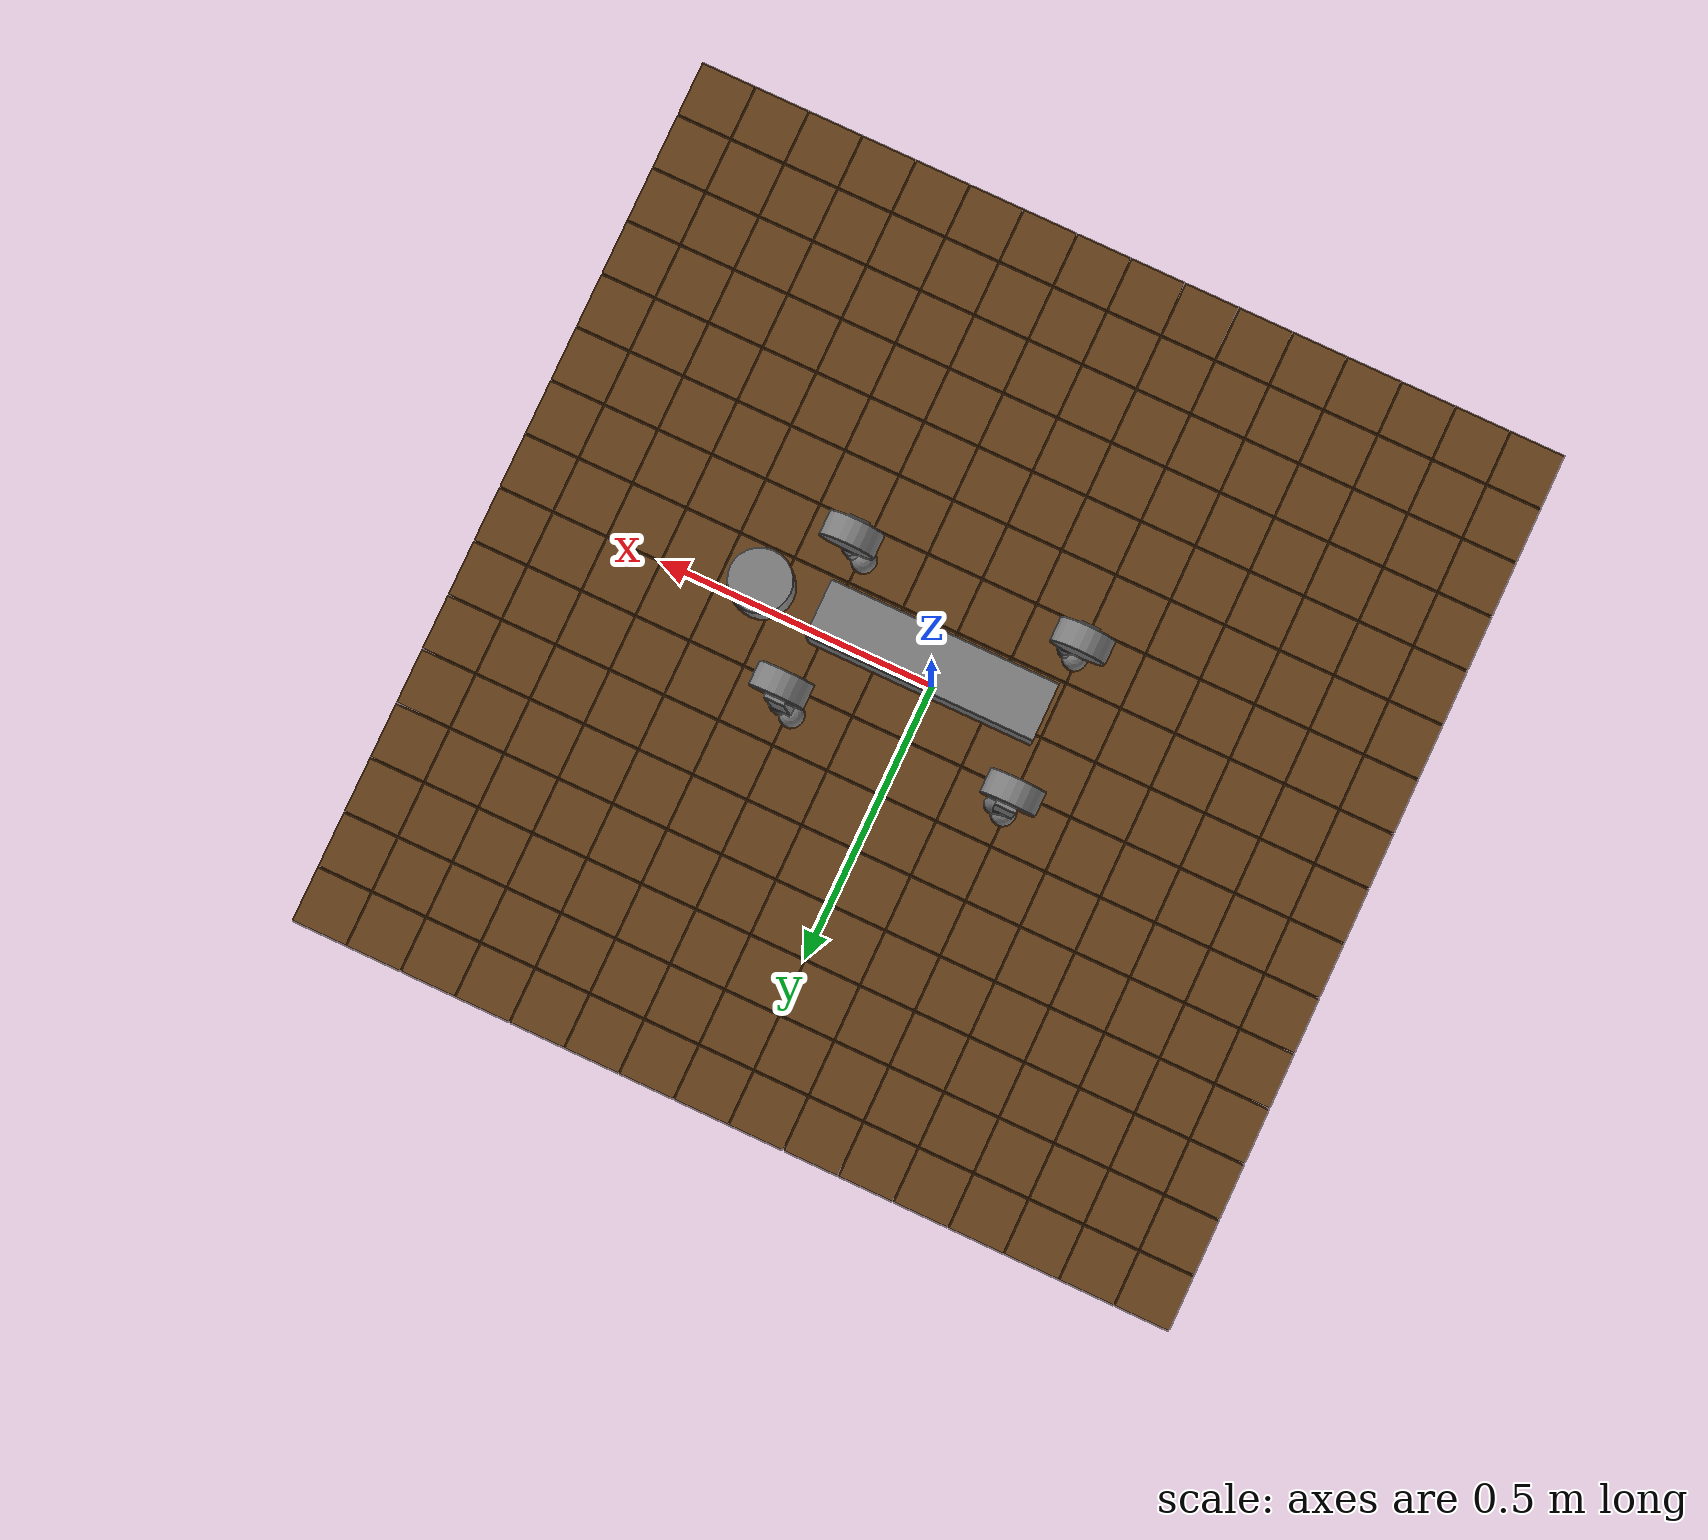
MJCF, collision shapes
<mujoco model="go2 scene">
  <include file="go2.xml" />

  <statistic center="0 0 0.1" extent="0.8" />

  <visual>
    <headlight diffuse="0.6 0.6 0.6" ambient="0.3 0.3 0.3" specular="0 0 0" />
    <rgba haze="0.15 0.25 0.35 1" />
    <global azimuth="-130" elevation="-20" />
    <map znear="0.01" zfar="100"/>
  </visual>

  <worldbody>
    <light pos="0 0 1.5" dir="0 0 -1" directional="true" />
    <!-- 16x16 dynamic ground grid: each box 0.1 x 0.1 x 1 (half-sizes 0.05 0.05 0.5) -->
    <!-- grid centers from -0.75 to 0.75 step 0.1 -->
    <body name="gb_0_0" pos="-0.75 -0.75 0" gravcomp="1">
      <joint type="free" name="gb_joint_0_0"/>
      <geom name="soil_0_0" type="box" size="0.049 0.049 0.5" pos="0 0 -0.5" rgba="0.40 0.25 0.10 1" mass="100000000"/>
    </body>
    <body name="gb_0_1" pos="-0.75 -0.65 0" gravcomp="1">
      <joint type="free" name="gb_joint_0_1"/>
      <geom name="soil_0_1" type="box" size="0.049 0.049 0.5" pos="0 0 -0.5" rgba="0.40 0.25 0.10 1" mass="100000000"/>
    </body>
    <body name="gb_0_2" pos="-0.75 -0.55 0" gravcomp="1">
      <joint type="free" name="gb_joint_0_2"/>
      <geom name="soil_0_2" type="box" size="0.049 0.049 0.5" pos="0 0 -0.5" rgba="0.40 0.25 0.10 1" mass="100000000"/>
    </body>
    <body name="gb_0_3" pos="-0.75 -0.45 0" gravcomp="1">
      <joint type="free" name="gb_joint_0_3"/>
      <geom name="soil_0_3" type="box" size="0.049 0.049 0.5" pos="0 0 -0.5" rgba="0.40 0.25 0.10 1" mass="100000000"/>
    </body>
    <body name="gb_0_4" pos="-0.75 -0.35 0" gravcomp="1">
      <joint type="free" name="gb_joint_0_4"/>
      <geom name="soil_0_4" type="box" size="0.049 0.049 0.5" pos="0 0 -0.5" rgba="0.40 0.25 0.10 1" mass="100000000"/>
    </body>
    <body name="gb_0_5" pos="-0.75 -0.25 0" gravcomp="1">
      <joint type="free" name="gb_joint_0_5"/>
      <geom name="soil_0_5" type="box" size="0.049 0.049 0.5" pos="0 0 -0.5" rgba="0.40 0.25 0.10 1" mass="100000000"/>
    </body>
    <body name="gb_0_6" pos="-0.75 -0.15 0" gravcomp="1">
      <joint type="free" name="gb_joint_0_6"/>
      <geom name="soil_0_6" type="box" size="0.049 0.049 0.5" pos="0 0 -0.5" rgba="0.40 0.25 0.10 1" mass="100000000"/>
    </body>
    <body name="gb_0_7" pos="-0.75 -0.05 0" gravcomp="1">
      <joint type="free" name="gb_joint_0_7"/>
      <geom name="soil_0_7" type="box" size="0.049 0.049 0.5" pos="0 0 -0.5" rgba="0.40 0.25 0.10 1" mass="100000000"/>
    </body>
    <body name="gb_0_8" pos="-0.75 0.05 0" gravcomp="1">
      <joint type="free" name="gb_joint_0_8"/>
      <geom name="soil_0_8" type="box" size="0.049 0.049 0.5" pos="0 0 -0.5" rgba="0.40 0.25 0.10 1" mass="100000000"/>
    </body>
    <body name="gb_0_9" pos="-0.75 0.15 0" gravcomp="1">
      <joint type="free" name="gb_joint_0_9"/>
      <geom name="soil_0_9" type="box" size="0.049 0.049 0.5" pos="0 0 -0.5" rgba="0.40 0.25 0.10 1" mass="100000000"/>
    </body>
    <body name="gb_0_10" pos="-0.75 0.25 0" gravcomp="1">
      <joint type="free" name="gb_joint_0_10"/>
      <geom name="soil_0_10" type="box" size="0.049 0.049 0.5" pos="0 0 -0.5" rgba="0.40 0.25 0.10 1" mass="100000000"/>
    </body>
    <body name="gb_0_11" pos="-0.75 0.35 0" gravcomp="1">
      <joint type="free" name="gb_joint_0_11"/>
      <geom name="soil_0_11" type="box" size="0.049 0.049 0.5" pos="0 0 -0.5" rgba="0.40 0.25 0.10 1" mass="100000000"/>
    </body>
    <body name="gb_0_12" pos="-0.75 0.45 0" gravcomp="1">
      <joint type="free" name="gb_joint_0_12"/>
      <geom name="soil_0_12" type="box" size="0.049 0.049 0.5" pos="0 0 -0.5" rgba="0.40 0.25 0.10 1" mass="100000000"/>
    </body>
    <body name="gb_0_13" pos="-0.75 0.55 0" gravcomp="1">
      <joint type="free" name="gb_joint_0_13"/>
      <geom name="soil_0_13" type="box" size="0.049 0.049 0.5" pos="0 0 -0.5" rgba="0.40 0.25 0.10 1" mass="100000000"/>
    </body>
    <body name="gb_0_14" pos="-0.75 0.65 0" gravcomp="1">
      <joint type="free" name="gb_joint_0_14"/>
      <geom name="soil_0_14" type="box" size="0.049 0.049 0.5" pos="0 0 -0.5" rgba="0.40 0.25 0.10 1" mass="100000000"/>
    </body>
    <body name="gb_0_15" pos="-0.75 0.75 0" gravcomp="1">
      <joint type="free" name="gb_joint_0_15"/>
      <geom name="soil_0_15" type="box" size="0.049 0.049 0.5" pos="0 0 -0.5" rgba="0.40 0.25 0.10 1" mass="100000000"/>
    </body>

    <body name="gb_1_0" pos="-0.65 -0.75 0" gravcomp="1">
      <joint type="free" name="gb_joint_1_0"/>
      <geom name="soil_1_0" type="box" size="0.049 0.049 0.5" pos="0 0 -0.5" rgba="0.40 0.25 0.10 1" mass="100000000"/>
    </body>
    <body name="gb_1_1" pos="-0.65 -0.65 0" gravcomp="1">
      <joint type="free" name="gb_joint_1_1"/>
      <geom name="soil_1_1" type="box" size="0.049 0.049 0.5" pos="0 0 -0.5" rgba="0.40 0.25 0.10 1" mass="100000000"/>
    </body>
    <body name="gb_1_2" pos="-0.65 -0.55 0" gravcomp="1">
      <joint type="free" name="gb_joint_1_2"/>
      <geom name="soil_1_2" type="box" size="0.049 0.049 0.5" pos="0 0 -0.5" rgba="0.40 0.25 0.10 1" mass="100000000"/>
    </body>
    <body name="gb_1_3" pos="-0.65 -0.45 0" gravcomp="1">
      <joint type="free" name="gb_joint_1_3"/>
      <geom name="soil_1_3" type="box" size="0.049 0.049 0.5" pos="0 0 -0.5" rgba="0.40 0.25 0.10 1" mass="100000000"/>
    </body>
    <body name="gb_1_4" pos="-0.65 -0.35 0" gravcomp="1">
      <joint type="free" name="gb_joint_1_4"/>
      <geom name="soil_1_4" type="box" size="0.049 0.049 0.5" pos="0 0 -0.5" rgba="0.40 0.25 0.10 1" mass="100000000"/>
    </body>
    <body name="gb_1_5" pos="-0.65 -0.25 0" gravcomp="1">
      <joint type="free" name="gb_joint_1_5"/>
      <geom name="soil_1_5" type="box" size="0.049 0.049 0.5" pos="0 0 -0.5" rgba="0.40 0.25 0.10 1" mass="100000000"/>
    </body>
    <body name="gb_1_6" pos="-0.65 -0.15 0" gravcomp="1">
      <joint type="free" name="gb_joint_1_6"/>
      <geom name="soil_1_6" type="box" size="0.049 0.049 0.5" pos="0 0 -0.5" rgba="0.40 0.25 0.10 1" mass="100000000"/>
    </body>
    <body name="gb_1_7" pos="-0.65 -0.05 0" gravcomp="1">
      <joint type="free" name="gb_joint_1_7"/>
      <geom name="soil_1_7" type="box" size="0.049 0.049 0.5" pos="0 0 -0.5" rgba="0.40 0.25 0.10 1" mass="100000000"/>
    </body>
    <body name="gb_1_8" pos="-0.65 0.05 0" gravcomp="1">
      <joint type="free" name="gb_joint_1_8"/>
      <geom name="soil_1_8" type="box" size="0.049 0.049 0.5" pos="0 0 -0.5" rgba="0.40 0.25 0.10 1" mass="100000000"/>
    </body>
    <body name="gb_1_9" pos="-0.65 0.15 0" gravcomp="1">
      <joint type="free" name="gb_joint_1_9"/>
      <geom name="soil_1_9" type="box" size="0.049 0.049 0.5" pos="0 0 -0.5" rgba="0.40 0.25 0.10 1" mass="100000000"/>
    </body>
    <body name="gb_1_10" pos="-0.65 0.25 0" gravcomp="1">
      <joint type="free" name="gb_joint_1_10"/>
      <geom name="soil_1_10" type="box" size="0.049 0.049 0.5" pos="0 0 -0.5" rgba="0.40 0.25 0.10 1" mass="100000000"/>
    </body>
    <body name="gb_1_11" pos="-0.65 0.35 0" gravcomp="1">
      <joint type="free" name="gb_joint_1_11"/>
      <geom name="soil_1_11" type="box" size="0.049 0.049 0.5" pos="0 0 -0.5" rgba="0.40 0.25 0.10 1" mass="100000000"/>
    </body>
    <body name="gb_1_12" pos="-0.65 0.45 0" gravcomp="1">
      <joint type="free" name="gb_joint_1_12"/>
      <geom name="soil_1_12" type="box" size="0.049 0.049 0.5" pos="0 0 -0.5" rgba="0.40 0.25 0.10 1" mass="100000000"/>
    </body>
    <body name="gb_1_13" pos="-0.65 0.55 0" gravcomp="1">
      <joint type="free" name="gb_joint_1_13"/>
      <geom name="soil_1_13" type="box" size="0.049 0.049 0.5" pos="0 0 -0.5" rgba="0.40 0.25 0.10 1" mass="100000000"/>
    </body>
    <body name="gb_1_14" pos="-0.65 0.65 0" gravcomp="1">
      <joint type="free" name="gb_joint_1_14"/>
      <geom name="soil_1_14" type="box" size="0.049 0.049 0.5" pos="0 0 -0.5" rgba="0.40 0.25 0.10 1" mass="100000000"/>
    </body>
    <body name="gb_1_15" pos="-0.65 0.75 0" gravcomp="1">
      <joint type="free" name="gb_joint_1_15"/>
      <geom name="soil_1_15" type="box" size="0.049 0.049 0.5" pos="0 0 -0.5" rgba="0.40 0.25 0.10 1" mass="100000000"/>
    </body>

    <body name="gb_2_0" pos="-0.55 -0.75 0" gravcomp="1">
      <joint type="free" name="gb_joint_2_0"/>
      <geom name="soil_2_0" type="box" size="0.049 0.049 0.5" pos="0 0 -0.5" rgba="0.40 0.25 0.10 1" mass="100000000"/>
    </body>
    <body name="gb_2_1" pos="-0.55 -0.65 0" gravcomp="1">
      <joint type="free" name="gb_joint_2_1"/>
      <geom name="soil_2_1" type="box" size="0.049 0.049 0.5" pos="0 0 -0.5" rgba="0.40 0.25 0.10 1" mass="100000000"/>
    </body>
    <body name="gb_2_2" pos="-0.55 -0.55 0" gravcomp="1">
      <joint type="free" name="gb_joint_2_2"/>
      <geom name="soil_2_2" type="box" size="0.049 0.049 0.5" pos="0 0 -0.5" rgba="0.40 0.25 0.10 1" mass="100000000"/>
    </body>
    <body name="gb_2_3" pos="-0.55 -0.45 0" gravcomp="1">
      <joint type="free" name="gb_joint_2_3"/>
      <geom name="soil_2_3" type="box" size="0.049 0.049 0.5" pos="0 0 -0.5" rgba="0.40 0.25 0.10 1" mass="100000000"/>
    </body>
    <body name="gb_2_4" pos="-0.55 -0.35 0" gravcomp="1">
      <joint type="free" name="gb_joint_2_4"/>
      <geom name="soil_2_4" type="box" size="0.049 0.049 0.5" pos="0 0 -0.5" rgba="0.40 0.25 0.10 1" mass="100000000"/>
    </body>
    <body name="gb_2_5" pos="-0.55 -0.25 0" gravcomp="1">
      <joint type="free" name="gb_joint_2_5"/>
      <geom name="soil_2_5" type="box" size="0.049 0.049 0.5" pos="0 0 -0.5" rgba="0.40 0.25 0.10 1" mass="100000000"/>
    </body>
    <body name="gb_2_6" pos="-0.55 -0.15 0" gravcomp="1">
      <joint type="free" name="gb_joint_2_6"/>
      <geom name="soil_2_6" type="box" size="0.049 0.049 0.5" pos="0 0 -0.5" rgba="0.40 0.25 0.10 1" mass="100000000"/>
    </body>
    <body name="gb_2_7" pos="-0.55 -0.05 0" gravcomp="1">
      <joint type="free" name="gb_joint_2_7"/>
      <geom name="soil_2_7" type="box" size="0.049 0.049 0.5" pos="0 0 -0.5" rgba="0.40 0.25 0.10 1" mass="100000000"/>
    </body>
    <body name="gb_2_8" pos="-0.55 0.05 0" gravcomp="1">
      <joint type="free" name="gb_joint_2_8"/>
      <geom name="soil_2_8" type="box" size="0.049 0.049 0.5" pos="0 0 -0.5" rgba="0.40 0.25 0.10 1" mass="100000000"/>
    </body>
    <body name="gb_2_9" pos="-0.55 0.15 0" gravcomp="1">
      <joint type="free" name="gb_joint_2_9"/>
      <geom name="soil_2_9" type="box" size="0.049 0.049 0.5" pos="0 0 -0.5" rgba="0.40 0.25 0.10 1" mass="100000000"/>
    </body>
    <body name="gb_2_10" pos="-0.55 0.25 0" gravcomp="1">
      <joint type="free" name="gb_joint_2_10"/>
      <geom name="soil_2_10" type="box" size="0.049 0.049 0.5" pos="0 0 -0.5" rgba="0.40 0.25 0.10 1" mass="100000000"/>
    </body>
    <body name="gb_2_11" pos="-0.55 0.35 0" gravcomp="1">
      <joint type="free" name="gb_joint_2_11"/>
      <geom name="soil_2_11" type="box" size="0.049 0.049 0.5" pos="0 0 -0.5" rgba="0.40 0.25 0.10 1" mass="100000000"/>
    </body>
    <body name="gb_2_12" pos="-0.55 0.45 0" gravcomp="1">
      <joint type="free" name="gb_joint_2_12"/>
      <geom name="soil_2_12" type="box" size="0.049 0.049 0.5" pos="0 0 -0.5" rgba="0.40 0.25 0.10 1" mass="100000000"/>
    </body>
    <body name="gb_2_13" pos="-0.55 0.55 0" gravcomp="1">
      <joint type="free" name="gb_joint_2_13"/>
      <geom name="soil_2_13" type="box" size="0.049 0.049 0.5" pos="0 0 -0.5" rgba="0.40 0.25 0.10 1" mass="100000000"/>
    </body>
    <body name="gb_2_14" pos="-0.55 0.65 0" gravcomp="1">
      <joint type="free" name="gb_joint_2_14"/>
      <geom name="soil_2_14" type="box" size="0.049 0.049 0.5" pos="0 0 -0.5" rgba="0.40 0.25 0.10 1" mass="100000000"/>
    </body>
    <body name="gb_2_15" pos="-0.55 0.75 0" gravcomp="1">
      <joint type="free" name="gb_joint_2_15"/>
      <geom name="soil_2_15" type="box" size="0.049 0.049 0.5" pos="0 0 -0.5" rgba="0.40 0.25 0.10 1" mass="100000000"/>
    </body>

    <body name="gb_3_0" pos="-0.45 -0.75 0" gravcomp="1">
      <joint type="free" name="gb_joint_3_0"/>
      <geom name="soil_3_0" type="box" size="0.049 0.049 0.5" pos="0 0 -0.5" rgba="0.40 0.25 0.10 1" mass="100000000"/>
    </body>
    <body name="gb_3_1" pos="-0.45 -0.65 0" gravcomp="1">
      <joint type="free" name="gb_joint_3_1"/>
      <geom name="soil_3_1" type="box" size="0.049 0.049 0.5" pos="0 0 -0.5" rgba="0.40 0.25 0.10 1" mass="100000000"/>
    </body>
    <body name="gb_3_2" pos="-0.45 -0.55 0" gravcomp="1">
      <joint type="free" name="gb_joint_3_2"/>
      <geom name="soil_3_2" type="box" size="0.049 0.049 0.5" pos="0 0 -0.5" rgba="0.40 0.25 0.10 1" mass="100000000"/>
    </body>
    <body name="gb_3_3" pos="-0.45 -0.45 0" gravcomp="1">
      <joint type="free" name="gb_joint_3_3"/>
      <geom name="soil_3_3" type="box" size="0.049 0.049 0.5" pos="0 0 -0.5" rgba="0.40 0.25 0.10 1" mass="100000000"/>
    </body>
    <body name="gb_3_4" pos="-0.45 -0.35 0" gravcomp="1">
      <joint type="free" name="gb_joint_3_4"/>
      <geom name="soil_3_4" type="box" size="0.049 0.049 0.5" pos="0 0 -0.5" rgba="0.40 0.25 0.10 1" mass="100000000"/>
    </body>
    <body name="gb_3_5" pos="-0.45 -0.25 0" gravcomp="1">
      <joint type="free" name="gb_joint_3_5"/>
      <geom name="soil_3_5" type="box" size="0.049 0.049 0.5" pos="0 0 -0.5" rgba="0.40 0.25 0.10 1" mass="100000000"/>
    </body>
    <body name="gb_3_6" pos="-0.45 -0.15 0" gravcomp="1">
      <joint type="free" name="gb_joint_3_6"/>
      <geom name="soil_3_6" type="box" size="0.049 0.049 0.5" pos="0 0 -0.5" rgba="0.40 0.25 0.10 1" mass="100000000"/>
    </body>
    <body name="gb_3_7" pos="-0.45 -0.05 0" gravcomp="1">
      <joint type="free" name="gb_joint_3_7"/>
      <geom name="soil_3_7" type="box" size="0.049 0.049 0.5" pos="0 0 -0.5" rgba="0.40 0.25 0.10 1" mass="100000000"/>
    </body>
    <body name="gb_3_8" pos="-0.45 0.05 0" gravcomp="1">
      <joint type="free" name="gb_joint_3_8"/>
      <geom name="soil_3_8" type="box" size="0.049 0.049 0.5" pos="0 0 -0.5" rgba="0.40 0.25 0.10 1" mass="100000000"/>
    </body>
    <body name="gb_3_9" pos="-0.45 0.15 0" gravcomp="1">
      <joint type="free" name="gb_joint_3_9"/>
      <geom name="soil_3_9" type="box" size="0.049 0.049 0.5" pos="0 0 -0.5" rgba="0.40 0.25 0.10 1" mass="100000000"/>
    </body>
    <body name="gb_3_10" pos="-0.45 0.25 0" gravcomp="1">
      <joint type="free" name="gb_joint_3_10"/>
      <geom name="soil_3_10" type="box" size="0.049 0.049 0.5" pos="0 0 -0.5" rgba="0.40 0.25 0.10 1" mass="100000000"/>
    </body>
    <body name="gb_3_11" pos="-0.45 0.35 0" gravcomp="1">
      <joint type="free" name="gb_joint_3_11"/>
      <geom name="soil_3_11" type="box" size="0.049 0.049 0.5" pos="0 0 -0.5" rgba="0.40 0.25 0.10 1" mass="100000000"/>
    </body>
    <body name="gb_3_12" pos="-0.45 0.45 0" gravcomp="1">
      <joint type="free" name="gb_joint_3_12"/>
      <geom name="soil_3_12" type="box" size="0.049 0.049 0.5" pos="0 0 -0.5" rgba="0.40 0.25 0.10 1" mass="100000000"/>
    </body>
    <body name="gb_3_13" pos="-0.45 0.55 0" gravcomp="1">
      <joint type="free" name="gb_joint_3_13"/>
      <geom name="soil_3_13" type="box" size="0.049 0.049 0.5" pos="0 0 -0.5" rgba="0.40 0.25 0.10 1" mass="100000000"/>
    </body>
    <body name="gb_3_14" pos="-0.45 0.65 0" gravcomp="1">
      <joint type="free" name="gb_joint_3_14"/>
      <geom name="soil_3_14" type="box" size="0.049 0.049 0.5" pos="0 0 -0.5" rgba="0.40 0.25 0.10 1" mass="100000000"/>
    </body>
    <body name="gb_3_15" pos="-0.45 0.75 0" gravcomp="1">
      <joint type="free" name="gb_joint_3_15"/>
      <geom name="soil_3_15" type="box" size="0.049 0.049 0.5" pos="0 0 -0.5" rgba="0.40 0.25 0.10 1" mass="100000000"/>
    </body>

    <body name="gb_4_0" pos="-0.35 -0.75 0" gravcomp="1">
      <joint type="free" name="gb_joint_4_0"/>
      <geom name="soil_4_0" type="box" size="0.049 0.049 0.5" pos="0 0 -0.5" rgba="0.40 0.25 0.10 1" mass="100000000"/>
    </body>
    <body name="gb_4_1" pos="-0.35 -0.65 0" gravcomp="1">
      <joint type="free" name="gb_joint_4_1"/>
      <geom name="soil_4_1" type="box" size="0.049 0.049 0.5" pos="0 0 -0.5" rgba="0.40 0.25 0.10 1" mass="100000000"/>
    </body>
    <body name="gb_4_2" pos="-0.35 -0.55 0" gravcomp="1">
      <joint type="free" name="gb_joint_4_2"/>
      <geom name="soil_4_2" type="box" size="0.049 0.049 0.5" pos="0 0 -0.5" rgba="0.40 0.25 0.10 1" mass="100000000"/>
    </body>
    <body name="gb_4_3" pos="-0.35 -0.45 0" gravcomp="1">
      <joint type="free" name="gb_joint_4_3"/>
      <geom name="soil_4_3" type="box" size="0.049 0.049 0.5" pos="0 0 -0.5" rgba="0.40 0.25 0.10 1" mass="100000000"/>
    </body>
    <body name="gb_4_4" pos="-0.35 -0.35 0" gravcomp="1">
      <joint type="free" name="gb_joint_4_4"/>
      <geom name="soil_4_4" type="box" size="0.049 0.049 0.5" pos="0 0 -0.5" rgba="0.40 0.25 0.10 1" mass="100000000"/>
    </body>
    <body name="gb_4_5" pos="-0.35 -0.25 0" gravcomp="1">
      <joint type="free" name="gb_joint_4_5"/>
      <geom name="soil_4_5" type="box" size="0.049 0.049 0.5" pos="0 0 -0.5" rgba="0.40 0.25 0.10 1" mass="100000000"/>
    </body>
    <body name="gb_4_6" pos="-0.35 -0.15 0" gravcomp="1">
      <joint type="free" name="gb_joint_4_6"/>
      <geom name="soil_4_6" type="box" size="0.049 0.049 0.5" pos="0 0 -0.5" rgba="0.40 0.25 0.10 1" mass="100000000"/>
    </body>
    <body name="gb_4_7" pos="-0.35 -0.05 0" gravcomp="1">
      <joint type="free" name="gb_joint_4_7"/>
      <geom name="soil_4_7" type="box" size="0.049 0.049 0.5" pos="0 0 -0.5" rgba="0.40 0.25 0.10 1" mass="100000000"/>
    </body>
    <body name="gb_4_8" pos="-0.35 0.05 0" gravcomp="1">
      <joint type="free" name="gb_joint_4_8"/>
      <geom name="soil_4_8" type="box" size="0.049 0.049 0.5" pos="0 0 -0.5" rgba="0.40 0.25 0.10 1" mass="100000000"/>
    </body>
    <body name="gb_4_9" pos="-0.35 0.15 0" gravcomp="1">
      <joint type="free" name="gb_joint_4_9"/>
      <geom name="soil_4_9" type="box" size="0.049 0.049 0.5" pos="0 0 -0.5" rgba="0.40 0.25 0.10 1" mass="100000000"/>
    </body>
    <body name="gb_4_10" pos="-0.35 0.25 0" gravcomp="1">
      <joint type="free" name="gb_joint_4_10"/>
      <geom name="soil_4_10" type="box" size="0.049 0.049 0.5" pos="0 0 -0.5" rgba="0.40 0.25 0.10 1" mass="100000000"/>
    </body>
    <body name="gb_4_11" pos="-0.35 0.35 0" gravcomp="1">
      <joint type="free" name="gb_joint_4_11"/>
      <geom name="soil_4_11" type="box" size="0.049 0.049 0.5" pos="0 0 -0.5" rgba="0.40 0.25 0.10 1" mass="100000000"/>
    </body>
    <body name="gb_4_12" pos="-0.35 0.45 0" gravcomp="1">
      <joint type="free" name="gb_joint_4_12"/>
      <geom name="soil_4_12" type="box" size="0.049 0.049 0.5" pos="0 0 -0.5" rgba="0.40 0.25 0.10 1" mass="100000000"/>
    </body>
    <body name="gb_4_13" pos="-0.35 0.55 0" gravcomp="1">
      <joint type="free" name="gb_joint_4_13"/>
      <geom name="soil_4_13" type="box" size="0.049 0.049 0.5" pos="0 0 -0.5" rgba="0.40 0.25 0.10 1" mass="100000000"/>
    </body>
    <body name="gb_4_14" pos="-0.35 0.65 0" gravcomp="1">
      <joint type="free" name="gb_joint_4_14"/>
      <geom name="soil_4_14" type="box" size="0.049 0.049 0.5" pos="0 0 -0.5" rgba="0.40 0.25 0.10 1" mass="100000000"/>
    </body>
    <body name="gb_4_15" pos="-0.35 0.75 0" gravcomp="1">
      <joint type="free" name="gb_joint_4_15"/>
      <geom name="soil_4_15" type="box" size="0.049 0.049 0.5" pos="0 0 -0.5" rgba="0.40 0.25 0.10 1" mass="100000000"/>
    </body>

    <body name="gb_5_0" pos="-0.25 -0.75 0" gravcomp="1">
      <joint type="free" name="gb_joint_5_0"/>
      <geom name="soil_5_0" type="box" size="0.049 0.049 0.5" pos="0 0 -0.5" rgba="0.40 0.25 0.10 1" mass="100000000"/>
    </body>
    <body name="gb_5_1" pos="-0.25 -0.65 0" gravcomp="1">
      <joint type="free" name="gb_joint_5_1"/>
      <geom name="soil_5_1" type="box" size="0.049 0.049 0.5" pos="0 0 -0.5" rgba="0.40 0.25 0.10 1" mass="100000000"/>
    </body>
    <body name="gb_5_2" pos="-0.25 -0.55 0" gravcomp="1">
      <joint type="free" name="gb_joint_5_2"/>
      <geom name="soil_5_2" type="box" size="0.049 0.049 0.5" pos="0 0 -0.5" rgba="0.40 0.25 0.10 1" mass="100000000"/>
    </body>
    <body name="gb_5_3" pos="-0.25 -0.45 0" gravcomp="1">
      <joint type="free" name="gb_joint_5_3"/>
      <geom name="soil_5_3" type="box" size="0.049 0.049 0.5" pos="0 0 -0.5" rgba="0.40 0.25 0.10 1" mass="100000000"/>
    </body>
    <body name="gb_5_4" pos="-0.25 -0.35 0" gravcomp="1">
      <joint type="free" name="gb_joint_5_4"/>
      <geom name="soil_5_4" type="box" size="0.049 0.049 0.5" pos="0 0 -0.5" rgba="0.40 0.25 0.10 1" mass="100000000"/>
    </body>
    <body name="gb_5_5" pos="-0.25 -0.25 0" gravcomp="1">
      <joint type="free" name="gb_joint_5_5"/>
      <geom name="soil_5_5" type="box" size="0.049 0.049 0.5" pos="0 0 -0.5" rgba="0.40 0.25 0.10 1" mass="100000000"/>
    </body>
    <body name="gb_5_6" pos="-0.25 -0.15 0" gravcomp="1">
      <joint type="free" name="gb_joint_5_6"/>
      <geom name="soil_5_6" type="box" size="0.049 0.049 0.5" pos="0 0 -0.5" rgba="0.40 0.25 0.10 1" mass="100000000"/>
    </body>
    <body name="gb_5_7" pos="-0.25 -0.05 0" gravcomp="1">
      <joint type="free" name="gb_joint_5_7"/>
      <geom name="soil_5_7" type="box" size="0.049 0.049 0.5" pos="0 0 -0.5" rgba="0.40 0.25 0.10 1" mass="100000000"/>
    </body>
    <body name="gb_5_8" pos="-0.25 0.05 0" gravcomp="1">
      <joint type="free" name="gb_joint_5_8"/>
      <geom name="soil_5_8" type="box" size="0.049 0.049 0.5" pos="0 0 -0.5" rgba="0.40 0.25 0.10 1" mass="100000000"/>
    </body>
    <body name="gb_5_9" pos="-0.25 0.15 0" gravcomp="1">
      <joint type="free" name="gb_joint_5_9"/>
      <geom name="soil_5_9" type="box" size="0.049 0.049 0.5" pos="0 0 -0.5" rgba="0.40 0.25 0.10 1" mass="100000000"/>
    </body>
    <body name="gb_5_10" pos="-0.25 0.25 0" gravcomp="1">
      <joint type="free" name="gb_joint_5_10"/>
      <geom name="soil_5_10" type="box" size="0.049 0.049 0.5" pos="0 0 -0.5" rgba="0.40 0.25 0.10 1" mass="100000000"/>
    </body>
    <body name="gb_5_11" pos="-0.25 0.35 0" gravcomp="1">
      <joint type="free" name="gb_joint_5_11"/>
      <geom name="soil_5_11" type="box" size="0.049 0.049 0.5" pos="0 0 -0.5" rgba="0.40 0.25 0.10 1" mass="100000000"/>
    </body>
    <body name="gb_5_12" pos="-0.25 0.45 0" gravcomp="1">
      <joint type="free" name="gb_joint_5_12"/>
      <geom name="soil_5_12" type="box" size="0.049 0.049 0.5" pos="0 0 -0.5" rgba="0.40 0.25 0.10 1" mass="100000000"/>
    </body>
    <body name="gb_5_13" pos="-0.25 0.55 0" gravcomp="1">
      <joint type="free" name="gb_joint_5_13"/>
      <geom name="soil_5_13" type="box" size="0.049 0.049 0.5" pos="0 0 -0.5" rgba="0.40 0.25 0.10 1" mass="100000000"/>
    </body>
    <body name="gb_5_14" pos="-0.25 0.65 0" gravcomp="1">
      <joint type="free" name="gb_joint_5_14"/>
      <geom name="soil_5_14" type="box" size="0.049 0.049 0.5" pos="0 0 -0.5" rgba="0.40 0.25 0.10 1" mass="100000000"/>
    </body>
    <body name="gb_5_15" pos="-0.25 0.75 0" gravcomp="1">
      <joint type="free" name="gb_joint_5_15"/>
      <geom name="soil_5_15" type="box" size="0.049 0.049 0.5" pos="0 0 -0.5" rgba="0.40 0.25 0.10 1" mass="100000000"/>
    </body>

    <body name="gb_6_0" pos="-0.15 -0.75 0" gravcomp="1">
      <joint type="free" name="gb_joint_6_0"/>
      <geom name="soil_6_0" type="box" size="0.049 0.049 0.5" pos="0 0 -0.5" rgba="0.40 0.25 0.10 1" mass="100000000"/>
    </body>
    <body name="gb_6_1" pos="-0.15 -0.65 0" gravcomp="1">
      <joint type="free" name="gb_joint_6_1"/>
      <geom name="soil_6_1" type="box" size="0.049 0.049 0.5" pos="0 0 -0.5" rgba="0.40 0.25 0.10 1" mass="100000000"/>
    </body>
    <body name="gb_6_2" pos="-0.15 -0.55 0" gravcomp="1">
      <joint type="free" name="gb_joint_6_2"/>
      <geom name="soil_6_2" type="box" size="0.049 0.049 0.5" pos="0 0 -0.5" rgba="0.40 0.25 0.10 1" mass="100000000"/>
    </body>
    <body name="gb_6_3" pos="-0.15 -0.45 0" gravcomp="1">
      <joint type="free" name="gb_joint_6_3"/>
      <geom name="soil_6_3" type="box" size="0.049 0.049 0.5" pos="0 0 -0.5" rgba="0.40 0.25 0.10 1" mass="100000000"/>
    </body>
    <body name="gb_6_4" pos="-0.15 -0.35 0" gravcomp="1">
      <joint type="free" name="gb_joint_6_4"/>
      <geom name="soil_6_4" type="box" size="0.049 0.049 0.5" pos="0 0 -0.5" rgba="0.40 0.25 0.10 1" mass="100000000"/>
    </body>
    <body name="gb_6_5" pos="-0.15 -0.25 0" gravcomp="1">
      <joint type="free" name="gb_joint_6_5"/>
      <geom name="soil_6_5" type="box" size="0.049 0.049 0.5" pos="0 0 -0.5" rgba="0.40 0.25 0.10 1" mass="100000000"/>
    </body>
    <body name="gb_6_6" pos="-0.15 -0.15 0" gravcomp="1">
      <joint type="free" name="gb_joint_6_6"/>
      <geom name="soil_6_6" type="box" size="0.049 0.049 0.5" pos="0 0 -0.5" rgba="0.40 0.25 0.10 1" mass="100000000"/>
    </body>
    <body name="gb_6_7" pos="-0.15 -0.05 0" gravcomp="1">
      <joint type="free" name="gb_joint_6_7"/>
      <geom name="soil_6_7" type="box" size="0.049 0.049 0.5" pos="0 0 -0.5" rgba="0.40 0.25 0.10 1" mass="100000000"/>
    </body>
    <body name="gb_6_8" pos="-0.15 0.05 0" gravcomp="1">
      <joint type="free" name="gb_joint_6_8"/>
      <geom name="soil_6_8" type="box" size="0.049 0.049 0.5" pos="0 0 -0.5" rgba="0.40 0.25 0.10 1" mass="100000000"/>
    </body>
    <body name="gb_6_9" pos="-0.15 0.15 0" gravcomp="1">
      <joint type="free" name="gb_joint_6_9"/>
      <geom name="soil_6_9" type="box" size="0.049 0.049 0.5" pos="0 0 -0.5" rgba="0.40 0.25 0.10 1" mass="100000000"/>
    </body>
    <body name="gb_6_10" pos="-0.15 0.25 0" gravcomp="1">
      <joint type="free" name="gb_joint_6_10"/>
      <geom name="soil_6_10" type="box" size="0.049 0.049 0.5" pos="0 0 -0.5" rgba="0.40 0.25 0.10 1" mass="100000000"/>
    </body>
    <body name="gb_6_11" pos="-0.15 0.35 0" gravcomp="1">
      <joint type="free" name="gb_joint_6_11"/>
      <geom name="soil_6_11" type="box" size="0.049 0.049 0.5" pos="0 0 -0.5" rgba="0.40 0.25 0.10 1" mass="100000000"/>
    </body>
    <body name="gb_6_12" pos="-0.15 0.45 0" gravcomp="1">
      <joint type="free" name="gb_joint_6_12"/>
      <geom name="soil_6_12" type="box" size="0.049 0.049 0.5" pos="0 0 -0.5" rgba="0.40 0.25 0.10 1" mass="100000000"/>
    </body>
    <body name="gb_6_13" pos="-0.15 0.55 0" gravcomp="1">
      <joint type="free" name="gb_joint_6_13"/>
      <geom name="soil_6_13" type="box" size="0.049 0.049 0.5" pos="0 0 -0.5" rgba="0.40 0.25 0.10 1" mass="100000000"/>
    </body>
    <body name="gb_6_14" pos="-0.15 0.65 0" gravcomp="1">
      <joint type="free" name="gb_joint_6_14"/>
      <geom name="soil_6_14" type="box" size="0.049 0.049 0.5" pos="0 0 -0.5" rgba="0.40 0.25 0.10 1" mass="100000000"/>
    </body>
    <body name="gb_6_15" pos="-0.15 0.75 0" gravcomp="1">
      <joint type="free" name="gb_joint_6_15"/>
      <geom name="soil_6_15" type="box" size="0.049 0.049 0.5" pos="0 0 -0.5" rgba="0.40 0.25 0.10 1" mass="100000000"/>
    </body>

    <body name="gb_7_0" pos="-0.05 -0.75 0" gravcomp="1">
      <joint type="free" name="gb_joint_7_0"/>
      <geom name="soil_7_0" type="box" size="0.049 0.049 0.5" pos="0 0 -0.5" rgba="0.40 0.25 0.10 1" mass="100000000"/>
    </body>
    <body name="gb_7_1" pos="-0.05 -0.65 0" gravcomp="1">
      <joint type="free" name="gb_joint_7_1"/>
      <geom name="soil_7_1" type="box" size="0.049 0.049 0.5" pos="0 0 -0.5" rgba="0.40 0.25 0.10 1" mass="100000000"/>
    </body>
    <body name="gb_7_2" pos="-0.05 -0.55 0" gravcomp="1">
      <joint type="free" name="gb_joint_7_2"/>
      <geom name="soil_7_2" type="box" size="0.049 0.049 0.5" pos="0 0 -0.5" rgba="0.40 0.25 0.10 1" mass="100000000"/>
    </body>
    <body name="gb_7_3" pos="-0.05 -0.45 0" gravcomp="1">
      <joint type="free" name="gb_joint_7_3"/>
      <geom name="soil_7_3" type="box" size="0.049 0.049 0.5" pos="0 0 -0.5" rgba="0.40 0.25 0.10 1" mass="100000000"/>
    </body>
    <body name="gb_7_4" pos="-0.05 -0.35 0" gravcomp="1">
      <joint type="free" name="gb_joint_7_4"/>
      <geom name="soil_7_4" type="box" size="0.049 0.049 0.5" pos="0 0 -0.5" rgba="0.40 0.25 0.10 1" mass="100000000"/>
    </body>
    <body name="gb_7_5" pos="-0.05 -0.25 0" gravcomp="1">
      <joint type="free" name="gb_joint_7_5"/>
      <geom name="soil_7_5" type="box" size="0.049 0.049 0.5" pos="0 0 -0.5" rgba="0.40 0.25 0.10 1" mass="100000000"/>
    </body>
    <body name="gb_7_6" pos="-0.05 -0.15 0" gravcomp="1">
      <joint type="free" name="gb_joint_7_6"/>
      <geom name="soil_7_6" type="box" size="0.049 0.049 0.5" pos="0 0 -0.5" rgba="0.40 0.25 0.10 1" mass="100000000"/>
    </body>
    <body name="gb_7_7" pos="-0.05 -0.05 0" gravcomp="1">
      <joint type="free" name="gb_joint_7_7"/>
      <geom name="soil_7_7" type="box" size="0.049 0.049 0.5" pos="0 0 -0.5" rgba="0.40 0.25 0.10 1" mass="100000000"/>
    </body>
    <body name="gb_7_8" pos="-0.05 0.05 0" gravcomp="1">
      <joint type="free" name="gb_joint_7_8"/>
      <geom name="soil_7_8" type="box" size="0.049 0.049 0.5" pos="0 0 -0.5" rgba="0.40 0.25 0.10 1" mass="100000000"/>
    </body>
    <body name="gb_7_9" pos="-0.05 0.15 0" gravcomp="1">
      <joint type="free" name="gb_joint_7_9"/>
      <geom name="soil_7_9" type="box" size="0.049 0.049 0.5" pos="0 0 -0.5" rgba="0.40 0.25 0.10 1" mass="100000000"/>
    </body>
    <body name="gb_7_10" pos="-0.05 0.25 0" gravcomp="1">
      <joint type="free" name="gb_joint_7_10"/>
      <geom name="soil_7_10" type="box" size="0.049 0.049 0.5" pos="0 0 -0.5" rgba="0.40 0.25 0.10 1" mass="100000000"/>
    </body>
    <body name="gb_7_11" pos="-0.05 0.35 0" gravcomp="1">
      <joint type="free" name="gb_joint_7_11"/>
      <geom name="soil_7_11" type="box" size="0.049 0.049 0.5" pos="0 0 -0.5" rgba="0.40 0.25 0.10 1" mass="100000000"/>
    </body>
    <body name="gb_7_12" pos="-0.05 0.45 0" gravcomp="1">
      <joint type="free" name="gb_joint_7_12"/>
      <geom name="soil_7_12" type="box" size="0.049 0.049 0.5" pos="0 0 -0.5" rgba="0.40 0.25 0.10 1" mass="100000000"/>
    </body>
    <body name="gb_7_13" pos="-0.05 0.55 0" gravcomp="1">
      <joint type="free" name="gb_joint_7_13"/>
      <geom name="soil_7_13" type="box" size="0.049 0.049 0.5" pos="0 0 -0.5" rgba="0.40 0.25 0.10 1" mass="100000000"/>
    </body>
    <body name="gb_7_14" pos="-0.05 0.65 0" gravcomp="1">
      <joint type="free" name="gb_joint_7_14"/>
      <geom name="soil_7_14" type="box" size="0.049 0.049 0.5" pos="0 0 -0.5" rgba="0.40 0.25 0.10 1" mass="100000000"/>
    </body>
    <body name="gb_7_15" pos="-0.05 0.75 0" gravcomp="1">
      <joint type="free" name="gb_joint_7_15"/>
      <geom name="soil_7_15" type="box" size="0.049 0.049 0.5" pos="0 0 -0.5" rgba="0.40 0.25 0.10 1" mass="100000000"/>
    </body>

    <body name="gb_8_0" pos="0.05 -0.75 0" gravcomp="1">
      <joint type="free" name="gb_joint_8_0"/>
      <geom name="soil_8_0" type="box" size="0.049 0.049 0.5" pos="0 0 -0.5" rgba="0.40 0.25 0.10 1" mass="100000000"/>
    </body>
    <body name="gb_8_1" pos="0.05 -0.65 0" gravcomp="1">
      <joint type="free" name="gb_joint_8_1"/>
      <geom name="soil_8_1" type="box" size="0.049 0.049 0.5" pos="0 0 -0.5" rgba="0.40 0.25 0.10 1" mass="100000000"/>
    </body>
    <body name="gb_8_2" pos="0.05 -0.55 0" gravcomp="1">
      <joint type="free" name="gb_joint_8_2"/>
      <geom name="soil_8_2" type="box" size="0.049 0.049 0.5" pos="0 0 -0.5" rgba="0.40 0.25 0.10 1" mass="100000000"/>
    </body>
    <body name="gb_8_3" pos="0.05 -0.45 0" gravcomp="1">
      <joint type="free" name="gb_joint_8_3"/>
      <geom name="soil_8_3" type="box" size="0.049 0.049 0.5" pos="0 0 -0.5" rgba="0.40 0.25 0.10 1" mass="100000000"/>
    </body>
    <body name="gb_8_4" pos="0.05 -0.35 0" gravcomp="1">
      <joint type="free" name="gb_joint_8_4"/>
      <geom name="soil_8_4" type="box" size="0.049 0.049 0.5" pos="0 0 -0.5" rgba="0.40 0.25 0.10 1" mass="100000000"/>
    </body>
    <body name="gb_8_5" pos="0.05 -0.25 0" gravcomp="1">
      <joint type="free" name="gb_joint_8_5"/>
      <geom name="soil_8_5" type="box" size="0.049 0.049 0.5" pos="0 0 -0.5" rgba="0.40 0.25 0.10 1" mass="100000000"/>
    </body>
    <body name="gb_8_6" pos="0.05 -0.15 0" gravcomp="1">
      <joint type="free" name="gb_joint_8_6"/>
      <geom name="soil_8_6" type="box" size="0.049 0.049 0.5" pos="0 0 -0.5" rgba="0.40 0.25 0.10 1" mass="100000000"/>
    </body>
    <body name="gb_8_7" pos="0.05 -0.05 0" gravcomp="1">
      <joint type="free" name="gb_joint_8_7"/>
      <geom name="soil_8_7" type="box" size="0.049 0.049 0.5" pos="0 0 -0.5" rgba="0.40 0.25 0.10 1" mass="100000000"/>
    </body>
    <body name="gb_8_8" pos="0.05 0.05 0" gravcomp="1">
      <joint type="free" name="gb_joint_8_8"/>
      <geom name="soil_8_8" type="box" size="0.049 0.049 0.5" pos="0 0 -0.5" rgba="0.40 0.25 0.10 1" mass="100000000"/>
    </body>
    <body name="gb_8_9" pos="0.05 0.15 0" gravcomp="1">
      <joint type="free" name="gb_joint_8_9"/>
      <geom name="soil_8_9" type="box" size="0.049 0.049 0.5" pos="0 0 -0.5" rgba="0.40 0.25 0.10 1" mass="100000000"/>
    </body>
    <body name="gb_8_10" pos="0.05 0.25 0" gravcomp="1">
      <joint type="free" name="gb_joint_8_10"/>
      <geom name="soil_8_10" type="box" size="0.049 0.049 0.5" pos="0 0 -0.5" rgba="0.40 0.25 0.10 1" mass="100000000"/>
    </body>
    <body name="gb_8_11" pos="0.05 0.35 0" gravcomp="1">
      <joint type="free" name="gb_joint_8_11"/>
      <geom name="soil_8_11" type="box" size="0.049 0.049 0.5" pos="0 0 -0.5" rgba="0.40 0.25 0.10 1" mass="100000000"/>
    </body>
    <body name="gb_8_12" pos="0.05 0.45 0" gravcomp="1">
      <joint type="free" name="gb_joint_8_12"/>
      <geom name="soil_8_12" type="box" size="0.049 0.049 0.5" pos="0 0 -0.5" rgba="0.40 0.25 0.10 1" mass="100000000"/>
    </body>
    <body name="gb_8_13" pos="0.05 0.55 0" gravcomp="1">
      <joint type="free" name="gb_joint_8_13"/>
      <geom name="soil_8_13" type="box" size="0.049 0.049 0.5" pos="0 0 -0.5" rgba="0.40 0.25 0.10 1" mass="100000000"/>
    </body>
    <body name="gb_8_14" pos="0.05 0.65 0" gravcomp="1">
      <joint type="free" name="gb_joint_8_14"/>
      <geom name="soil_8_14" type="box" size="0.049 0.049 0.5" pos="0 0 -0.5" rgba="0.40 0.25 0.10 1" mass="100000000"/>
    </body>
    <body name="gb_8_15" pos="0.05 0.75 0" gravcomp="1">
      <joint type="free" name="gb_joint_8_15"/>
      <geom name="soil_8_15" type="box" size="0.049 0.049 0.5" pos="0 0 -0.5" rgba="0.40 0.25 0.10 1" mass="100000000"/>
    </body>

    <body name="gb_9_0" pos="0.15 -0.75 0" gravcomp="1">
      <joint type="free" name="gb_joint_9_0"/>
      <geom name="soil_9_0" type="box" size="0.049 0.049 0.5" pos="0 0 -0.5" rgba="0.40 0.25 0.10 1" mass="100000000"/>
    </body>
    <body name="gb_9_1" pos="0.15 -0.65 0" gravcomp="1">
      <joint type="free" name="gb_joint_9_1"/>
      <geom name="soil_9_1" type="box" size="0.049 0.049 0.5" pos="0 0 -0.5" rgba="0.40 0.25 0.10 1" mass="100000000"/>
    </body>
    <body name="gb_9_2" pos="0.15 -0.55 0" gravcomp="1">
      <joint type="free" name="gb_joint_9_2"/>
      <geom name="soil_9_2" type="box" size="0.049 0.049 0.5" pos="0 0 -0.5" rgba="0.40 0.25 0.10 1" mass="100000000"/>
    </body>
    <body name="gb_9_3" pos="0.15 -0.45 0" gravcomp="1">
      <joint type="free" name="gb_joint_9_3"/>
      <geom name="soil_9_3" type="box" size="0.049 0.049 0.5" pos="0 0 -0.5" rgba="0.40 0.25 0.10 1" mass="100000000"/>
    </body>
    <body name="gb_9_4" pos="0.15 -0.35 0" gravcomp="1">
      <joint type="free" name="gb_joint_9_4"/>
      <geom name="soil_9_4" type="box" size="0.049 0.049 0.5" pos="0 0 -0.5" rgba="0.40 0.25 0.10 1" mass="100000000"/>
    </body>
    <body name="gb_9_5" pos="0.15 -0.25 0" gravcomp="1">
      <joint type="free" name="gb_joint_9_5"/>
      <geom name="soil_9_5" type="box" size="0.049 0.049 0.5" pos="0 0 -0.5" rgba="0.40 0.25 0.10 1" mass="100000000"/>
    </body>
    <body name="gb_9_6" pos="0.15 -0.15 0" gravcomp="1">
      <joint type="free" name="gb_joint_9_6"/>
      <geom name="soil_9_6" type="box" size="0.049 0.049 0.5" pos="0 0 -0.5" rgba="0.40 0.25 0.10 1" mass="100000000"/>
    </body>
    <body name="gb_9_7" pos="0.15 -0.05 0" gravcomp="1">
      <joint type="free" name="gb_joint_9_7"/>
      <geom name="soil_9_7" type="box" size="0.049 0.049 0.5" pos="0 0 -0.5" rgba="0.40 0.25 0.10 1" mass="100000000"/>
    </body>
    <body name="gb_9_8" pos="0.15 0.05 0" gravcomp="1">
      <joint type="free" name="gb_joint_9_8"/>
      <geom name="soil_9_8" type="box" size="0.049 0.049 0.5" pos="0 0 -0.5" rgba="0.40 0.25 0.10 1" mass="100000000"/>
    </body>
    <body name="gb_9_9" pos="0.15 0.15 0" gravcomp="1">
      <joint type="free" name="gb_joint_9_9"/>
      <geom name="soil_9_9" type="box" size="0.049 0.049 0.5" pos="0 0 -0.5" rgba="0.40 0.25 0.10 1" mass="100000000"/>
    </body>
    <body name="gb_9_10" pos="0.15 0.25 0" gravcomp="1">
      <joint type="free" name="gb_joint_9_10"/>
      <geom name="soil_9_10" type="box" size="0.049 0.049 0.5" pos="0 0 -0.5" rgba="0.40 0.25 0.10 1" mass="100000000"/>
    </body>
    <body name="gb_9_11" pos="0.15 0.35 0" gravcomp="1">
      <joint type="free" name="gb_joint_9_11"/>
      <geom name="soil_9_11" type="box" size="0.049 0.049 0.5" pos="0 0 -0.5" rgba="0.40 0.25 0.10 1" mass="100000000"/>
    </body>
    <body name="gb_9_12" pos="0.15 0.45 0" gravcomp="1">
      <joint type="free" name="gb_joint_9_12"/>
      <geom name="soil_9_12" type="box" size="0.049 0.049 0.5" pos="0 0 -0.5" rgba="0.40 0.25 0.10 1" mass="100000000"/>
    </body>
    <body name="gb_9_13" pos="0.15 0.55 0" gravcomp="1">
      <joint type="free" name="gb_joint_9_13"/>
      <geom name="soil_9_13" type="box" size="0.049 0.049 0.5" pos="0 0 -0.5" rgba="0.40 0.25 0.10 1" mass="100000000"/>
    </body>
    <body name="gb_9_14" pos="0.15 0.65 0" gravcomp="1">
      <joint type="free" name="gb_joint_9_14"/>
      <geom name="soil_9_14" type="box" size="0.049 0.049 0.5" pos="0 0 -0.5" rgba="0.40 0.25 0.10 1" mass="100000000"/>
    </body>
    <body name="gb_9_15" pos="0.15 0.75 0" gravcomp="1">
      <joint type="free" name="gb_joint_9_15"/>
      <geom name="soil_9_15" type="box" size="0.049 0.049 0.5" pos="0 0 -0.5" rgba="0.40 0.25 0.10 1" mass="100000000"/>
    </body>

    <body name="gb_10_0" pos="0.25 -0.75 0" gravcomp="1">
      <joint type="free" name="gb_joint_10_0"/>
      <geom name="soil_10_0" type="box" size="0.049 0.049 0.5" pos="0 0 -0.5" rgba="0.40 0.25 0.10 1" mass="100000000"/>
    </body>
    <body name="gb_10_1" pos="0.25 -0.65 0" gravcomp="1">
      <joint type="free" name="gb_joint_10_1"/>
      <geom name="soil_10_1" type="box" size="0.049 0.049 0.5" pos="0 0 -0.5" rgba="0.40 0.25 0.10 1" mass="100000000"/>
    </body>
    <body name="gb_10_2" pos="0.25 -0.55 0" gravcomp="1">
      <joint type="free" name="gb_joint_10_2"/>
      <geom name="soil_10_2" type="box" size="0.049 0.049 0.5" pos="0 0 -0.5" rgba="0.40 0.25 0.10 1" mass="100000000"/>
    </body>
    <body name="gb_10_3" pos="0.25 -0.45 0" gravcomp="1">
      <joint type="free" name="gb_joint_10_3"/>
      <geom name="soil_10_3" type="box" size="0.049 0.049 0.5" pos="0 0 -0.5" rgba="0.40 0.25 0.10 1" mass="100000000"/>
    </body>
    <body name="gb_10_4" pos="0.25 -0.35 0" gravcomp="1">
      <joint type="free" name="gb_joint_10_4"/>
      <geom name="soil_10_4" type="box" size="0.049 0.049 0.5" pos="0 0 -0.5" rgba="0.40 0.25 0.10 1" mass="100000000"/>
    </body>
    <body name="gb_10_5" pos="0.25 -0.25 0" gravcomp="1">
      <joint type="free" name="gb_joint_10_5"/>
      <geom name="soil_10_5" type="box" size="0.049 0.049 0.5" pos="0 0 -0.5" rgba="0.40 0.25 0.10 1" mass="100000000"/>
    </body>
    <body name="gb_10_6" pos="0.25 -0.15 0" gravcomp="1">
      <joint type="free" name="gb_joint_10_6"/>
      <geom name="soil_10_6" type="box" size="0.049 0.049 0.5" pos="0 0 -0.5" rgba="0.40 0.25 0.10 1" mass="100000000"/>
    </body>
    <body name="gb_10_7" pos="0.25 -0.05 0" gravcomp="1">
      <joint type="free" name="gb_joint_10_7"/>
      <geom name="soil_10_7" type="box" size="0.049 0.049 0.5" pos="0 0 -0.5" rgba="0.40 0.25 0.10 1" mass="100000000"/>
    </body>
    <body name="gb_10_8" pos="0.25 0.05 0" gravcomp="1">
      <joint type="free" name="gb_joint_10_8"/>
      <geom name="soil_10_8" type="box" size="0.049 0.049 0.5" pos="0 0 -0.5" rgba="0.40 0.25 0.10 1" mass="100000000"/>
    </body>
    <body name="gb_10_9" pos="0.25 0.15 0" gravcomp="1">
      <joint type="free" name="gb_joint_10_9"/>
      <geom name="soil_10_9" type="box" size="0.049 0.049 0.5" pos="0 0 -0.5" rgba="0.40 0.25 0.10 1" mass="100000000"/>
    </body>
    <body name="gb_10_10" pos="0.25 0.25 0" gravcomp="1">
      <joint type="free" name="gb_joint_10_10"/>
      <geom name="soil_10_10" type="box" size="0.049 0.049 0.5" pos="0 0 -0.5" rgba="0.40 0.25 0.10 1" mass="100000000"/>
    </body>
    <body name="gb_10_11" pos="0.25 0.35 0" gravcomp="1">
      <joint type="free" name="gb_joint_10_11"/>
      <geom name="soil_10_11" type="box" size="0.049 0.049 0.5" pos="0 0 -0.5" rgba="0.40 0.25 0.10 1" mass="100000000"/>
    </body>
    <body name="gb_10_12" pos="0.25 0.45 0" gravcomp="1">
      <joint type="free" name="gb_joint_10_12"/>
      <geom name="soil_10_12" type="box" size="0.049 0.049 0.5" pos="0 0 -0.5" rgba="0.40 0.25 0.10 1" mass="100000000"/>
    </body>
    <body name="gb_10_13" pos="0.25 0.55 0" gravcomp="1">
      <joint type="free" name="gb_joint_10_13"/>
      <geom name="soil_10_13" type="box" size="0.049 0.049 0.5" pos="0 0 -0.5" rgba="0.40 0.25 0.10 1" mass="100000000"/>
    </body>
    <body name="gb_10_14" pos="0.25 0.65 0" gravcomp="1">
      <joint type="free" name="gb_joint_10_14"/>
      <geom name="soil_10_14" type="box" size="0.049 0.049 0.5" pos="0 0 -0.5" rgba="0.40 0.25 0.10 1" mass="100000000"/>
    </body>
    <body name="gb_10_15" pos="0.25 0.75 0" gravcomp="1">
      <joint type="free" name="gb_joint_10_15"/>
      <geom name="soil_10_15" type="box" size="0.049 0.049 0.5" pos="0 0 -0.5" rgba="0.40 0.25 0.10 1" mass="100000000"/>
    </body>

    <body name="gb_11_0" pos="0.35 -0.75 0" gravcomp="1">
      <joint type="free" name="gb_joint_11_0"/>
      <geom name="soil_11_0" type="box" size="0.049 0.049 0.5" pos="0 0 -0.5" rgba="0.40 0.25 0.10 1" mass="100000000"/>
    </body>
    <body name="gb_11_1" pos="0.35 -0.65 0" gravcomp="1">
      <joint type="free" name="gb_joint_11_1"/>
      <geom name="soil_11_1" type="box" size="0.049 0.049 0.5" pos="0 0 -0.5" rgba="0.40 0.25 0.10 1" mass="100000000"/>
    </body>
    <body name="gb_11_2" pos="0.35 -0.55 0" gravcomp="1">
      <joint type="free" name="gb_joint_11_2"/>
      <geom name="soil_11_2" type="box" size="0.049 0.049 0.5" pos="0 0 -0.5" rgba="0.40 0.25 0.10 1" mass="100000000"/>
    </body>
    <body name="gb_11_3" pos="0.35 -0.45 0" gravcomp="1">
      <joint type="free" name="gb_joint_11_3"/>
      <geom name="soil_11_3" type="box" size="0.049 0.049 0.5" pos="0 0 -0.5" rgba="0.40 0.25 0.10 1" mass="100000000"/>
    </body>
    <body name="gb_11_4" pos="0.35 -0.35 0" gravcomp="1">
      <joint type="free" name="gb_joint_11_4"/>
      <geom name="soil_11_4" type="box" size="0.049 0.049 0.5" pos="0 0 -0.5" rgba="0.40 0.25 0.10 1" mass="100000000"/>
    </body>
    <body name="gb_11_5" pos="0.35 -0.25 0" gravcomp="1">
      <joint type="free" name="gb_joint_11_5"/>
      <geom name="soil_11_5" type="box" size="0.049 0.049 0.5" pos="0 0 -0.5" rgba="0.40 0.25 0.10 1" mass="100000000"/>
    </body>
    <body name="gb_11_6" pos="0.35 -0.15 0" gravcomp="1">
      <joint type="free" name="gb_joint_11_6"/>
      <geom name="soil_11_6" type="box" size="0.049 0.049 0.5" pos="0 0 -0.5" rgba="0.40 0.25 0.10 1" mass="100000000"/>
    </body>
    <body name="gb_11_7" pos="0.35 -0.05 0" gravcomp="1">
      <joint type="free" name="gb_joint_11_7"/>
      <geom name="soil_11_7" type="box" size="0.049 0.049 0.5" pos="0 0 -0.5" rgba="0.40 0.25 0.10 1" mass="100000000"/>
    </body>
    <body name="gb_11_8" pos="0.35 0.05 0" gravcomp="1">
      <joint type="free" name="gb_joint_11_8"/>
      <geom name="soil_11_8" type="box" size="0.049 0.049 0.5" pos="0 0 -0.5" rgba="0.40 0.25 0.10 1" mass="100000000"/>
    </body>
    <body name="gb_11_9" pos="0.35 0.15 0" gravcomp="1">
      <joint type="free" name="gb_joint_11_9"/>
      <geom name="soil_11_9" type="box" size="0.049 0.049 0.5" pos="0 0 -0.5" rgba="0.40 0.25 0.10 1" mass="100000000"/>
    </body>
    <body name="gb_11_10" pos="0.35 0.25 0" gravcomp="1">
      <joint type="free" name="gb_joint_11_10"/>
      <geom name="soil_11_10" type="box" size="0.049 0.049 0.5" pos="0 0 -0.5" rgba="0.40 0.25 0.10 1" mass="100000000"/>
    </body>
    <body name="gb_11_11" pos="0.35 0.35 0" gravcomp="1">
      <joint type="free" name="gb_joint_11_11"/>
      <geom name="soil_11_11" type="box" size="0.049 0.049 0.5" pos="0 0 -0.5" rgba="0.40 0.25 0.10 1" mass="100000000"/>
    </body>
    <body name="gb_11_12" pos="0.35 0.45 0" gravcomp="1">
      <joint type="free" name="gb_joint_11_12"/>
      <geom name="soil_11_12" type="box" size="0.049 0.049 0.5" pos="0 0 -0.5" rgba="0.40 0.25 0.10 1" mass="100000000"/>
    </body>
    <body name="gb_11_13" pos="0.35 0.55 0" gravcomp="1">
      <joint type="free" name="gb_joint_11_13"/>
      <geom name="soil_11_13" type="box" size="0.049 0.049 0.5" pos="0 0 -0.5" rgba="0.40 0.25 0.10 1" mass="100000000"/>
    </body>
    <body name="gb_11_14" pos="0.35 0.65 0" gravcomp="1">
      <joint type="free" name="gb_joint_11_14"/>
      <geom name="soil_11_14" type="box" size="0.049 0.049 0.5" pos="0 0 -0.5" rgba="0.40 0.25 0.10 1" mass="100000000"/>
    </body>
    <body name="gb_11_15" pos="0.35 0.75 0" gravcomp="1">
      <joint type="free" name="gb_joint_11_15"/>
      <geom name="soil_11_15" type="box" size="0.049 0.049 0.5" pos="0 0 -0.5" rgba="0.40 0.25 0.10 1" mass="100000000"/>
    </body>

    <body name="gb_12_0" pos="0.45 -0.75 0" gravcomp="1">
      <joint type="free" name="gb_joint_12_0"/>
      <geom name="soil_12_0" type="box" size="0.049 0.049 0.5" pos="0 0 -0.5" rgba="0.40 0.25 0.10 1" mass="100000000"/>
    </body>
    <body name="gb_12_1" pos="0.45 -0.65 0" gravcomp="1">
      <joint type="free" name="gb_joint_12_1"/>
      <geom name="soil_12_1" type="box" size="0.049 0.049 0.5" pos="0 0 -0.5" rgba="0.40 0.25 0.10 1" mass="100000000"/>
    </body>
    <body name="gb_12_2" pos="0.45 -0.55 0" gravcomp="1">
      <joint type="free" name="gb_joint_12_2"/>
      <geom name="soil_12_2" type="box" size="0.049 0.049 0.5" pos="0 0 -0.5" rgba="0.40 0.25 0.10 1" mass="100000000"/>
    </body>
    <body name="gb_12_3" pos="0.45 -0.45 0" gravcomp="1">
      <joint type="free" name="gb_joint_12_3"/>
      <geom name="soil_12_3" type="box" size="0.049 0.049 0.5" pos="0 0 -0.5" rgba="0.40 0.25 0.10 1" mass="100000000"/>
    </body>
    <body name="gb_12_4" pos="0.45 -0.35 0" gravcomp="1">
      <joint type="free" name="gb_joint_12_4"/>
      <geom name="soil_12_4" type="box" size="0.049 0.049 0.5" pos="0 0 -0.5" rgba="0.40 0.25 0.10 1" mass="100000000"/>
    </body>
    <body name="gb_12_5" pos="0.45 -0.25 0" gravcomp="1">
      <joint type="free" name="gb_joint_12_5"/>
      <geom name="soil_12_5" type="box" size="0.049 0.049 0.5" pos="0 0 -0.5" rgba="0.40 0.25 0.10 1" mass="100000000"/>
    </body>
    <body name="gb_12_6" pos="0.45 -0.15 0" gravcomp="1">
      <joint type="free" name="gb_joint_12_6"/>
      <geom name="soil_12_6" type="box" size="0.049 0.049 0.5" pos="0 0 -0.5" rgba="0.40 0.25 0.10 1" mass="100000000"/>
    </body>
    <body name="gb_12_7" pos="0.45 -0.05 0" gravcomp="1">
      <joint type="free" name="gb_joint_12_7"/>
      <geom name="soil_12_7" type="box" size="0.049 0.049 0.5" pos="0 0 -0.5" rgba="0.40 0.25 0.10 1" mass="100000000"/>
    </body>
    <body name="gb_12_8" pos="0.45 0.05 0" gravcomp="1">
      <joint type="free" name="gb_joint_12_8"/>
      <geom name="soil_12_8" type="box" size="0.049 0.049 0.5" pos="0 0 -0.5" rgba="0.40 0.25 0.10 1" mass="100000000"/>
    </body>
    <body name="gb_12_9" pos="0.45 0.15 0" gravcomp="1">
      <joint type="free" name="gb_joint_12_9"/>
      <geom name="soil_12_9" type="box" size="0.049 0.049 0.5" pos="0 0 -0.5" rgba="0.40 0.25 0.10 1" mass="100000000"/>
    </body>
    <body name="gb_12_10" pos="0.45 0.25 0" gravcomp="1">
      <joint type="free" name="gb_joint_12_10"/>
      <geom name="soil_12_10" type="box" size="0.049 0.049 0.5" pos="0 0 -0.5" rgba="0.40 0.25 0.10 1" mass="100000000"/>
    </body>
    <body name="gb_12_11" pos="0.45 0.35 0" gravcomp="1">
      <joint type="free" name="gb_joint_12_11"/>
      <geom name="soil_12_11" type="box" size="0.049 0.049 0.5" pos="0 0 -0.5" rgba="0.40 0.25 0.10 1" mass="100000000"/>
    </body>
    <body name="gb_12_12" pos="0.45 0.45 0" gravcomp="1">
      <joint type="free" name="gb_joint_12_12"/>
      <geom name="soil_12_12" type="box" size="0.049 0.049 0.5" pos="0 0 -0.5" rgba="0.40 0.25 0.10 1" mass="100000000"/>
    </body>
    <body name="gb_12_13" pos="0.45 0.55 0" gravcomp="1">
      <joint type="free" name="gb_joint_12_13"/>
      <geom name="soil_12_13" type="box" size="0.049 0.049 0.5" pos="0 0 -0.5" rgba="0.40 0.25 0.10 1" mass="100000000"/>
    </body>
    <body name="gb_12_14" pos="0.45 0.65 0" gravcomp="1">
      <joint type="free" name="gb_joint_12_14"/>
      <geom name="soil_12_14" type="box" size="0.049 0.049 0.5" pos="0 0 -0.5" rgba="0.40 0.25 0.10 1" mass="100000000"/>
    </body>
    <body name="gb_12_15" pos="0.45 0.75 0" gravcomp="1">
      <joint type="free" name="gb_joint_12_15"/>
      <geom name="soil_12_15" type="box" size="0.049 0.049 0.5" pos="0 0 -0.5" rgba="0.40 0.25 0.10 1" mass="100000000"/>
    </body>

    <body name="gb_13_0" pos="0.55 -0.75 0" gravcomp="1">
      <joint type="free" name="gb_joint_13_0"/>
      <geom name="soil_13_0" type="box" size="0.049 0.049 0.5" pos="0 0 -0.5" rgba="0.40 0.25 0.10 1" mass="100000000"/>
    </body>
    <body name="gb_13_1" pos="0.55 -0.65 0" gravcomp="1">
      <joint type="free" name="gb_joint_13_1"/>
      <geom name="soil_13_1" type="box" size="0.049 0.049 0.5" pos="0 0 -0.5" rgba="0.40 0.25 0.10 1" mass="100000000"/>
    </body>
    <body name="gb_13_2" pos="0.55 -0.55 0" gravcomp="1">
      <joint type="free" name="gb_joint_13_2"/>
      <geom name="soil_13_2" type="box" size="0.049 0.049 0.5" pos="0 0 -0.5" rgba="0.40 0.25 0.10 1" mass="100000000"/>
    </body>
    <body name="gb_13_3" pos="0.55 -0.45 0" gravcomp="1">
      <joint type="free" name="gb_joint_13_3"/>
      <geom name="soil_13_3" type="box" size="0.049 0.049 0.5" pos="0 0 -0.5" rgba="0.40 0.25 0.10 1" mass="100000000"/>
    </body>
    <body name="gb_13_4" pos="0.55 -0.35 0" gravcomp="1">
      <joint type="free" name="gb_joint_13_4"/>
      <geom name="soil_13_4" type="box" size="0.049 0.049 0.5" pos="0 0 -0.5" rgba="0.40 0.25 0.10 1" mass="100000000"/>
    </body>
    <body name="gb_13_5" pos="0.55 -0.25 0" gravcomp="1">
      <joint type="free" name="gb_joint_13_5"/>
      <geom name="soil_13_5" type="box" size="0.049 0.049 0.5" pos="0 0 -0.5" rgba="0.40 0.25 0.10 1" mass="100000000"/>
    </body>
    <body name="gb_13_6" pos="0.55 -0.15 0" gravcomp="1">
      <joint type="free" name="gb_joint_13_6"/>
      <geom name="soil_13_6" type="box" size="0.049 0.049 0.5" pos="0 0 -0.5" rgba="0.40 0.25 0.10 1" mass="100000000"/>
    </body>
    <body name="gb_13_7" pos="0.55 -0.05 0" gravcomp="1">
      <joint type="free" name="gb_joint_13_7"/>
      <geom name="soil_13_7" type="box" size="0.049 0.049 0.5" pos="0 0 -0.5" rgba="0.40 0.25 0.10 1" mass="100000000"/>
    </body>
    <body name="gb_13_8" pos="0.55 0.05 0" gravcomp="1">
      <joint type="free" name="gb_joint_13_8"/>
      <geom name="soil_13_8" type="box" size="0.049 0.049 0.5" pos="0 0 -0.5" rgba="0.40 0.25 0.10 1" mass="100000000"/>
    </body>
    <body name="gb_13_9" pos="0.55 0.15 0" gravcomp="1">
      <joint type="free" name="gb_joint_13_9"/>
      <geom name="soil_13_9" type="box" size="0.049 0.049 0.5" pos="0 0 -0.5" rgba="0.40 0.25 0.10 1" mass="100000000"/>
    </body>
    <body name="gb_13_10" pos="0.55 0.25 0" gravcomp="1">
      <joint type="free" name="gb_joint_13_10"/>
      <geom name="soil_13_10" type="box" size="0.049 0.049 0.5" pos="0 0 -0.5" rgba="0.40 0.25 0.10 1" mass="100000000"/>
    </body>
    <body name="gb_13_11" pos="0.55 0.35 0" gravcomp="1">
      <joint type="free" name="gb_joint_13_11"/>
      <geom name="soil_13_11" type="box" size="0.049 0.049 0.5" pos="0 0 -0.5" rgba="0.40 0.25 0.10 1" mass="100000000"/>
    </body>
    <body name="gb_13_12" pos="0.55 0.45 0" gravcomp="1">
      <joint type="free" name="gb_joint_13_12"/>
      <geom name="soil_13_12" type="box" size="0.049 0.049 0.5" pos="0 0 -0.5" rgba="0.40 0.25 0.10 1" mass="100000000"/>
    </body>
    <body name="gb_13_13" pos="0.55 0.55 0" gravcomp="1">
      <joint type="free" name="gb_joint_13_13"/>
      <geom name="soil_13_13" type="box" size="0.049 0.049 0.5" pos="0 0 -0.5" rgba="0.40 0.25 0.10 1" mass="100000000"/>
    </body>
    <body name="gb_13_14" pos="0.55 0.65 0" gravcomp="1">
      <joint type="free" name="gb_joint_13_14"/>
      <geom name="soil_13_14" type="box" size="0.049 0.049 0.5" pos="0 0 -0.5" rgba="0.40 0.25 0.10 1" mass="100000000"/>
    </body>
    <body name="gb_13_15" pos="0.55 0.75 0" gravcomp="1">
      <joint type="free" name="gb_joint_13_15"/>
      <geom name="soil_13_15" type="box" size="0.049 0.049 0.5" pos="0 0 -0.5" rgba="0.40 0.25 0.10 1" mass="100000000"/>
    </body>

    <body name="gb_14_0" pos="0.65 -0.75 0" gravcomp="1">
      <joint type="free" name="gb_joint_14_0"/>
      <geom name="soil_14_0" type="box" size="0.049 0.049 0.5" pos="0 0 -0.5" rgba="0.40 0.25 0.10 1" mass="100000000"/>
    </body>
    <body name="gb_14_1" pos="0.65 -0.65 0" gravcomp="1">
      <joint type="free" name="gb_joint_14_1"/>
      <geom name="soil_14_1" type="box" size="0.049 0.049 0.5" pos="0 0 -0.5" rgba="0.40 0.25 0.10 1" mass="100000000"/>
    </body>
    <body name="gb_14_2" pos="0.65 -0.55 0" gravcomp="1">
      <joint type="free" name="gb_joint_14_2"/>
      <geom name="soil_14_2" type="box" size="0.049 0.049 0.5" pos="0 0 -0.5" rgba="0.40 0.25 0.10 1" mass="100000000"/>
    </body>
    <body name="gb_14_3" pos="0.65 -0.45 0" gravcomp="1">
      <joint type="free" name="gb_joint_14_3"/>
      <geom name="soil_14_3" type="box" size="0.049 0.049 0.5" pos="0 0 -0.5" rgba="0.40 0.25 0.10 1" mass="100000000"/>
    </body>
    <body name="gb_14_4" pos="0.65 -0.35 0" gravcomp="1">
      <joint type="free" name="gb_joint_14_4"/>
      <geom name="soil_14_4" type="box" size="0.049 0.049 0.5" pos="0 0 -0.5" rgba="0.40 0.25 0.10 1" mass="100000000"/>
    </body>
    <body name="gb_14_5" pos="0.65 -0.25 0" gravcomp="1">
      <joint type="free" name="gb_joint_14_5"/>
      <geom name="soil_14_5" type="box" size="0.049 0.049 0.5" pos="0 0 -0.5" rgba="0.40 0.25 0.10 1" mass="100000000"/>
    </body>
    <body name="gb_14_6" pos="0.65 -0.15 0" gravcomp="1">
      <joint type="free" name="gb_joint_14_6"/>
      <geom name="soil_14_6" type="box" size="0.049 0.049 0.5" pos="0 0 -0.5" rgba="0.40 0.25 0.10 1" mass="100000000"/>
    </body>
    <body name="gb_14_7" pos="0.65 -0.05 0" gravcomp="1">
      <joint type="free" name="gb_joint_14_7"/>
      <geom name="soil_14_7" type="box" size="0.049 0.049 0.5" pos="0 0 -0.5" rgba="0.40 0.25 0.10 1" mass="100000000"/>
    </body>
    <body name="gb_14_8" pos="0.65 0.05 0" gravcomp="1">
      <joint type="free" name="gb_joint_14_8"/>
      <geom name="soil_14_8" type="box" size="0.049 0.049 0.5" pos="0 0 -0.5" rgba="0.40 0.25 0.10 1" mass="100000000"/>
    </body>
    <body name="gb_14_9" pos="0.65 0.15 0" gravcomp="1">
      <joint type="free" name="gb_joint_14_9"/>
      <geom name="soil_14_9" type="box" size="0.049 0.049 0.5" pos="0 0 -0.5" rgba="0.40 0.25 0.10 1" mass="100000000"/>
    </body>
    <body name="gb_14_10" pos="0.65 0.25 0" gravcomp="1">
      <joint type="free" name="gb_joint_14_10"/>
      <geom name="soil_14_10" type="box" size="0.049 0.049 0.5" pos="0 0 -0.5" rgba="0.40 0.25 0.10 1" mass="100000000"/>
    </body>
    <body name="gb_14_11" pos="0.65 0.35 0" gravcomp="1">
      <joint type="free" name="gb_joint_14_11"/>
      <geom name="soil_14_11" type="box" size="0.049 0.049 0.5" pos="0 0 -0.5" rgba="0.40 0.25 0.10 1" mass="100000000"/>
    </body>
    <body name="gb_14_12" pos="0.65 0.45 0" gravcomp="1">
      <joint type="free" name="gb_joint_14_12"/>
      <geom name="soil_14_12" type="box" size="0.049 0.049 0.5" pos="0 0 -0.5" rgba="0.40 0.25 0.10 1" mass="100000000"/>
    </body>
    <body name="gb_14_13" pos="0.65 0.55 0" gravcomp="1">
      <joint type="free" name="gb_joint_14_13"/>
      <geom name="soil_14_13" type="box" size="0.049 0.049 0.5" pos="0 0 -0.5" rgba="0.40 0.25 0.10 1" mass="100000000"/>
    </body>
    <body name="gb_14_14" pos="0.65 0.65 0" gravcomp="1">
      <joint type="free" name="gb_joint_14_14"/>
      <geom name="soil_14_14" type="box" size="0.049 0.049 0.5" pos="0 0 -0.5" rgba="0.40 0.25 0.10 1" mass="100000000"/>
    </body>
    <body name="gb_14_15" pos="0.65 0.75 0" gravcomp="1">
      <joint type="free" name="gb_joint_14_15"/>
      <geom name="soil_14_15" type="box" size="0.049 0.049 0.5" pos="0 0 -0.5" rgba="0.40 0.25 0.10 1" mass="100000000"/>
    </body>

    <body name="gb_15_0" pos="0.75 -0.75 0" gravcomp="1">
      <joint type="free" name="gb_joint_15_0"/>
      <geom name="soil_15_0" type="box" size="0.049 0.049 0.5" pos="0 0 -0.5" rgba="0.40 0.25 0.10 1" mass="100000000"/>
    </body>
    <body name="gb_15_1" pos="0.75 -0.65 0" gravcomp="1">
      <joint type="free" name="gb_joint_15_1"/>
      <geom name="soil_15_1" type="box" size="0.049 0.049 0.5" pos="0 0 -0.5" rgba="0.40 0.25 0.10 1" mass="100000000"/>
    </body>
    <body name="gb_15_2" pos="0.75 -0.55 0" gravcomp="1">
      <joint type="free" name="gb_joint_15_2"/>
      <geom name="soil_15_2" type="box" size="0.049 0.049 0.5" pos="0 0 -0.5" rgba="0.40 0.25 0.10 1" mass="100000000"/>
    </body>
    <body name="gb_15_3" pos="0.75 -0.45 0" gravcomp="1">
      <joint type="free" name="gb_joint_15_3"/>
      <geom name="soil_15_3" type="box" size="0.049 0.049 0.5" pos="0 0 -0.5" rgba="0.40 0.25 0.10 1" mass="100000000"/>
    </body>
    <body name="gb_15_4" pos="0.75 -0.35 0" gravcomp="1">
      <joint type="free" name="gb_joint_15_4"/>
      <geom name="soil_15_4" type="box" size="0.049 0.049 0.5" pos="0 0 -0.5" rgba="0.40 0.25 0.10 1" mass="100000000"/>
    </body>
    <body name="gb_15_5" pos="0.75 -0.25 0" gravcomp="1">
      <joint type="free" name="gb_joint_15_5"/>
      <geom name="soil_15_5" type="box" size="0.049 0.049 0.5" pos="0 0 -0.5" rgba="0.40 0.25 0.10 1" mass="100000000"/>
    </body>
    <body name="gb_15_6" pos="0.75 -0.15 0" gravcomp="1">
      <joint type="free" name="gb_joint_15_6"/>
      <geom name="soil_15_6" type="box" size="0.049 0.049 0.5" pos="0 0 -0.5" rgba="0.40 0.25 0.10 1" mass="100000000"/>
    </body>
    <body name="gb_15_7" pos="0.75 -0.05 0" gravcomp="1">
      <joint type="free" name="gb_joint_15_7"/>
      <geom name="soil_15_7" type="box" size="0.049 0.049 0.5" pos="0 0 -0.5" rgba="0.40 0.25 0.10 1" mass="100000000"/>
    </body>
    <body name="gb_15_8" pos="0.75 0.05 0" gravcomp="1">
      <joint type="free" name="gb_joint_15_8"/>
      <geom name="soil_15_8" type="box" size="0.049 0.049 0.5" pos="0 0 -0.5" rgba="0.40 0.25 0.10 1" mass="100000000"/>
    </body>
    <body name="gb_15_9" pos="0.75 0.15 0" gravcomp="1">
      <joint type="free" name="gb_joint_15_9"/>
      <geom name="soil_15_9" type="box" size="0.049 0.049 0.5" pos="0 0 -0.5" rgba="0.40 0.25 0.10 1" mass="100000000"/>
    </body>
    <body name="gb_15_10" pos="0.75 0.25 0" gravcomp="1">
      <joint type="free" name="gb_joint_15_10"/>
      <geom name="soil_15_10" type="box" size="0.049 0.049 0.5" pos="0 0 -0.5" rgba="0.40 0.25 0.10 1" mass="100000000"/>
    </body>
    <body name="gb_15_11" pos="0.75 0.35 0" gravcomp="1">
      <joint type="free" name="gb_joint_15_11"/>
      <geom name="soil_15_11" type="box" size="0.049 0.049 0.5" pos="0 0 -0.5" rgba="0.40 0.25 0.10 1" mass="100000000"/>
    </body>
    <body name="gb_15_12" pos="0.75 0.45 0" gravcomp="1">
      <joint type="free" name="gb_joint_15_12"/>
      <geom name="soil_15_12" type="box" size="0.049 0.049 0.5" pos="0 0 -0.5" rgba="0.40 0.25 0.10 1" mass="100000000"/>
    </body>
    <body name="gb_15_13" pos="0.75 0.55 0" gravcomp="1">
      <joint type="free" name="gb_joint_15_13"/>
      <geom name="soil_15_13" type="box" size="0.049 0.049 0.5" pos="0 0 -0.5" rgba="0.40 0.25 0.10 1" mass="100000000"/>
    </body>
    <body name="gb_15_14" pos="0.75 0.65 0" gravcomp="1">
      <joint type="free" name="gb_joint_15_14"/>
      <geom name="soil_15_14" type="box" size="0.049 0.049 0.5" pos="0 0 -0.5" rgba="0.40 0.25 0.10 1" mass="100000000"/>
    </body>
    <body name="gb_15_15" pos="0.75 0.75 0" gravcomp="1">
      <joint type="free" name="gb_joint_15_15"/>
      <geom name="soil_15_15" type="box" size="0.049 0.049 0.5" pos="0 0 -0.5" rgba="0.40 0.25 0.10 1" mass="100000000"/>
    </body>

    </worldbody>
</mujoco>

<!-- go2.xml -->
<mujoco model="go2">
  <compiler angle="radian" meshdir="assets" autolimits="true" />

  <option cone="elliptic" impratio="100" />

  <default>
    <default class="go2">
      <geom friction="0.4" margin="0.001" condim="1"/>
      <joint axis="0 1 0" damping="0.1" armature="0.01" frictionloss="0.2"/>
      <motor ctrlrange="-23.7 23.7"/>
      <default class="abduction">
        <joint axis="1 0 0" range="-1.0472 1.0472"/>
      </default>
      <default class="hip">
        <default class="front_hip">
          <joint range="-1.5708 3.4907"/>
        </default>
        <default class="back_hip">
          <joint range="-0.5236 4.5379"/>
        </default>
      </default>
      <default class="knee">
        <joint range="-2.7227 -0.83776"/>
        <motor ctrlrange="-45.43 45.43"/>
      </default>
      <default class="visual">
        <geom type="mesh" contype="0" conaffinity="0" group="2"/>
      </default>
      <default class="collision">
        <geom group="3"/>
        <default class="foot">
          <geom size="0.022" pos="-0.002 0 -0.213" priority="1" condim="6"
            friction="0.4 0.02 0.01"/>
        </default>
      </default>
    </default>
  </default>

  <asset>
    <material name="metal" rgba=".9 .95 .95 1" />
    <material name="black" rgba="0 0 0 1" />
    <material name="white" rgba="1 1 1 1" />
    <material name="gray" rgba="0.671705 0.692426 0.774270 1" />

    <mesh file="base_0.obj" />
    <mesh file="base_1.obj" />
    <mesh file="base_2.obj" />
    <mesh file="base_3.obj" />
    <mesh file="base_4.obj" />
    <mesh file="hip_0.obj" />
    <mesh file="hip_1.obj" />
    <mesh file="thigh_0.obj" />
    <mesh file="thigh_1.obj" />
    <mesh file="thigh_mirror_0.obj" />
    <mesh file="thigh_mirror_1.obj" />
    <mesh file="calf_0.obj" />
    <mesh file="calf_1.obj" />
    <mesh file="calf_mirror_0.obj" />
    <mesh file="calf_mirror_1.obj" />
    <mesh file="foot.obj" />
  </asset>

  <worldbody>
    <body name="base_link" pos="0 0 0.445" childclass="go2">
      <inertial pos="0.021112 0 -0.005366" quat="-0.000543471 0.713435 -0.00173769 0.700719"
        mass="6.921"
        diaginertia="0.107027 0.0980771 0.0244531" />
      <freejoint />
      <geom mesh="base_0" material="black" class="visual" />
      <geom mesh="base_1" material="black" class="visual" />
      <geom mesh="base_2" material="black" class="visual" />
      <geom mesh="base_3" material="white" class="visual" />
      <geom mesh="base_4" material="gray" class="visual" />
      <geom size="0.1881 0.04675 0.057" type="box" class="collision" />
      <geom size="0.05 0.045" pos="0.285 0 0.01" type="cylinder" class="collision" />
      <geom size="0.047" pos="0.293 0 -0.06" class="collision" />
      <site name="imu" pos="-0.02557 0 0.04232" />

      <body name="FL_hip" pos="0.1934 0.0465 0">
        <inertial pos="-0.0054 0.00194 -0.000105" quat="0.497014 0.499245 0.505462 0.498237"
          mass="0.678"
          diaginertia="0.00088403 0.000596003 0.000479967" />
        <joint name="FL_hip_joint" class="abduction" />
        <geom mesh="hip_0" material="metal" class="visual" />
        <geom mesh="hip_1" material="gray" class="visual" />
        <geom size="0.046 0.02" pos="0 0.08 0" quat="1 1 0 0" type="cylinder" class="collision" />
        <body name="FL_thigh" pos="0 0.0955 0">
          <inertial pos="-0.00374 -0.0223 -0.0327" quat="0.829533 0.0847635 -0.0200632 0.551623"
            mass="1.152"
            diaginertia="0.00594973 0.00584149 0.000878787" />
          <joint name="FL_thigh_joint" class="front_hip" />
          <geom mesh="thigh_0" material="metal" class="visual" />
          <geom mesh="thigh_1" material="gray" class="visual" />
          <geom size="0.1065 0.01225 0.017" pos="0 0 -0.1065" quat="0.707107 0 0.707107 0"
            type="box" class="collision" />
          <body name="FL_calf" pos="0 0 -0.213">
            <inertial pos="0.00629595 -0.000622121 -0.141417"
              quat="0.710672 0.00154099 -0.00450087 0.703508"
              mass="0.241352" diaginertia="0.0014901 0.00146356 5.31397e-05" />
            <joint name="FL_calf_joint" class="knee" />
            <geom mesh="calf_0" material="gray" class="visual" />
            <geom mesh="calf_1" material="black" class="visual" />
            <geom size="0.012 0.06" pos="0.008 0 -0.06" quat="0.994493 0 -0.104807 0"
              type="cylinder" class="collision" />
            <geom size="0.011 0.0325" pos="0.02 0 -0.148" quat="0.999688 0 0.0249974 0"
              type="cylinder" class="collision" />
            <geom pos="0 0 -0.213" mesh="foot" class="visual" material="black" />
            <geom name="FL" class="foot" />
            <body name="FL_foot" pos="0 0 -0.213" />
          </body>
        </body>
      </body>
      <body name="FR_hip" pos="0.1934 -0.0465 0">
        <inertial pos="-0.0054 -0.00194 -0.000105" quat="0.498237 0.505462 0.499245 0.497014"
          mass="0.678"
          diaginertia="0.00088403 0.000596003 0.000479967" />
        <joint name="FR_hip_joint" class="abduction" />
        <geom mesh="hip_0" material="metal" class="visual" quat="4.63268e-05 1 0 0" />
        <geom mesh="hip_1" material="gray" class="visual" quat="4.63268e-05 1 0 0" />
        <geom size="0.046 0.02" pos="0 -0.08 0" quat="0.707107 0.707107 0 0" type="cylinder"
          class="collision" />
        <body name="FR_thigh" pos="0 -0.0955 0">
          <inertial pos="-0.00374 0.0223 -0.0327" quat="0.551623 -0.0200632 0.0847635 0.829533"
            mass="1.152"
            diaginertia="0.00594973 0.00584149 0.000878787" />
          <joint name="FR_thigh_joint" class="front_hip" />
          <geom mesh="thigh_mirror_0" material="metal" class="visual" />
          <geom mesh="thigh_mirror_1" material="gray" class="visual" />
          <geom size="0.1065 0.01225 0.017" pos="0 0 -0.1065" quat="0.707107 0 0.707107 0"
            type="box" class="collision" />
          <body name="FR_calf" pos="0 0 -0.213">
            <inertial pos="0.00629595 0.000622121 -0.141417"
              quat="0.703508 -0.00450087 0.00154099 0.710672"
              mass="0.241352" diaginertia="0.0014901 0.00146356 5.31397e-05" />
            <joint name="FR_calf_joint" class="knee" />
            <geom mesh="calf_mirror_0" material="gray" class="visual" />
            <geom mesh="calf_mirror_1" material="black" class="visual" />
            <geom size="0.013 0.06" pos="0.01 0 -0.06" quat="0.995004 0 -0.0998334 0"
              type="cylinder" class="collision" />
            <geom size="0.011 0.0325" pos="0.02 0 -0.148" quat="0.999688 0 0.0249974 0"
              type="cylinder" class="collision" />
            <geom pos="0 0 -0.213" mesh="foot" class="visual" material="black" />
            <geom name="FR" class="foot" />
            <body name="FR_foot" pos="0 0 -0.213" />
          </body>
        </body>
      </body>
      <body name="RL_hip" pos="-0.1934 0.0465 0">
        <inertial pos="0.0054 0.00194 -0.000105" quat="0.505462 0.498237 0.497014 0.499245"
          mass="0.678"
          diaginertia="0.00088403 0.000596003 0.000479967" />
        <joint name="RL_hip_joint" class="abduction" />
        <geom mesh="hip_0" material="metal" class="visual" quat="4.63268e-05 0 1 0" />
        <geom mesh="hip_1" material="gray" class="visual" quat="4.63268e-05 0 1 0" />
        <geom size="0.046 0.02" pos="0 0.08 0" quat="0.707107 0.707107 0 0" type="cylinder"
          class="collision" />
        <body name="RL_thigh" pos="0 0.0955 0">
          <inertial pos="-0.00374 -0.0223 -0.0327" quat="0.829533 0.0847635 -0.0200632 0.551623"
            mass="1.152"
            diaginertia="0.00594973 0.00584149 0.000878787" />
          <joint name="RL_thigh_joint" class="back_hip" />
          <geom mesh="thigh_0" material="metal" class="visual" />
          <geom mesh="thigh_1" material="gray" class="visual" />
          <geom size="0.1065 0.01225 0.017" pos="0 0 -0.1065" quat="0.707107 0 0.707107 0"
            type="box" class="collision" />
          <body name="RL_calf" pos="0 0 -0.213">
            <inertial pos="0.00629595 -0.000622121 -0.141417"
              quat="0.710672 0.00154099 -0.00450087 0.703508"
              mass="0.241352" diaginertia="0.0014901 0.00146356 5.31397e-05" />
            <joint name="RL_calf_joint" class="knee" />
            <geom mesh="calf_0" material="gray" class="visual" />
            <geom mesh="calf_1" material="black" class="visual" />
            <geom size="0.013 0.06" pos="0.01 0 -0.06" quat="0.995004 0 -0.0998334 0"
              type="cylinder" class="collision" />
            <geom size="0.011 0.0325" pos="0.02 0 -0.148" quat="0.999688 0 0.0249974 0"
              type="cylinder" class="collision" />
            <geom pos="0 0 -0.213" mesh="foot" class="visual" material="black" />
            <geom name="RL" class="foot" />
            <body name="RL_foot" pos="0 0 -0.213" />
          </body>
        </body>
      </body>
      <body name="RR_hip" pos="-0.1934 -0.0465 0">
        <inertial pos="0.0054 -0.00194 -0.000105" quat="0.499245 0.497014 0.498237 0.505462"
          mass="0.678"
          diaginertia="0.00088403 0.000596003 0.000479967" />
        <joint name="RR_hip_joint" class="abduction" />
        <geom mesh="hip_0" material="metal" class="visual"
          quat="2.14617e-09 4.63268e-05 4.63268e-05 -1" />
        <geom mesh="hip_1" material="gray" class="visual"
          quat="2.14617e-09 4.63268e-05 4.63268e-05 -1" />
        <geom size="0.046 0.02" pos="0 -0.08 0" quat="0.707107 0.707107 0 0" type="cylinder"
          class="collision" />
        <body name="RR_thigh" pos="0 -0.0955 0">
          <inertial pos="-0.00374 0.0223 -0.0327" quat="0.551623 -0.0200632 0.0847635 0.829533"
            mass="1.152"
            diaginertia="0.00594973 0.00584149 0.000878787" />
          <joint name="RR_thigh_joint" class="back_hip" />
          <geom mesh="thigh_mirror_0" material="metal" class="visual" />
          <geom mesh="thigh_mirror_1" material="gray" class="visual" />
          <geom size="0.1065 0.01225 0.017" pos="0 0 -0.1065" quat="0.707107 0 0.707107 0"
            type="box" class="collision" />
          <body name="RR_calf" pos="0 0 -0.213">
            <inertial pos="0.00629595 0.000622121 -0.141417"
              quat="0.703508 -0.00450087 0.00154099 0.710672"
              mass="0.241352" diaginertia="0.0014901 0.00146356 5.31397e-05" />
            <joint name="RR_calf_joint" class="knee" />
            <geom mesh="calf_mirror_0" material="gray" class="visual" />
            <geom mesh="calf_mirror_1" material="black" class="visual" />
            <geom size="0.013 0.06" pos="0.01 0 -0.06" quat="0.995004 0 -0.0998334 0"
              type="cylinder" class="collision" />
            <geom size="0.011 0.0325" pos="0.02 0 -0.148" quat="0.999688 0 0.0249974 0"
              type="cylinder" class="collision" />
            <geom pos="0 0 -0.213" mesh="foot" class="visual" material="black" />
            <geom name="RR" class="foot" />
            <body name="RR_foot" pos="0 0 -0.213" />
          </body>
        </body>
      </body>
    </body>
  </worldbody>

  <actuator>
    <motor class="abduction" name="FR_hip" joint="FR_hip_joint" />
    <motor class="hip" name="FR_thigh" joint="FR_thigh_joint" />
    <motor class="knee" name="FR_calf" joint="FR_calf_joint" />
    <motor class="abduction" name="FL_hip" joint="FL_hip_joint" />
    <motor class="hip" name="FL_thigh" joint="FL_thigh_joint" />
    <motor class="knee" name="FL_calf" joint="FL_calf_joint" />
    <motor class="abduction" name="RR_hip" joint="RR_hip_joint" />
    <motor class="hip" name="RR_thigh" joint="RR_thigh_joint" />
    <motor class="knee" name="RR_calf" joint="RR_calf_joint" />
    <motor class="abduction" name="RL_hip" joint="RL_hip_joint" />
    <motor class="hip" name="RL_thigh" joint="RL_thigh_joint" />
    <motor class="knee" name="RL_calf" joint="RL_calf_joint" />
  </actuator>

  <sensor>
    <jointpos name="FR_hip_pos" joint="FR_hip_joint" />
    <jointpos name="FR_thigh_pos" joint="FR_thigh_joint" />
    <jointpos name="FR_calf_pos" joint="FR_calf_joint" />
    <jointpos name="FL_hip_pos" joint="FL_hip_joint" />
    <jointpos name="FL_thigh_pos" joint="FL_thigh_joint" />
    <jointpos name="FL_calf_pos" joint="FL_calf_joint" />
    <jointpos name="RR_hip_pos" joint="RR_hip_joint" />
    <jointpos name="RR_thigh_pos" joint="RR_thigh_joint" />
    <jointpos name="RR_calf_pos" joint="RR_calf_joint" />
    <jointpos name="RL_hip_pos" joint="RL_hip_joint" />
    <jointpos name="RL_thigh_pos" joint="RL_thigh_joint" />
    <jointpos name="RL_calf_pos" joint="RL_calf_joint" />

    <jointvel name="FR_hip_vel" joint="FR_hip_joint" />
    <jointvel name="FR_thigh_vel" joint="FR_thigh_joint" />
    <jointvel name="FR_calf_vel" joint="FR_calf_joint" />
    <jointvel name="FL_hip_vel" joint="FL_hip_joint" />
    <jointvel name="FL_thigh_vel" joint="FL_thigh_joint" />
    <jointvel name="FL_calf_vel" joint="FL_calf_joint" />
    <jointvel name="RR_hip_vel" joint="RR_hip_joint" />
    <jointvel name="RR_thigh_vel" joint="RR_thigh_joint" />
    <jointvel name="RR_calf_vel" joint="RR_calf_joint" />
    <jointvel name="RL_hip_vel" joint="RL_hip_joint" />
    <jointvel name="RL_thigh_vel" joint="RL_thigh_joint" />
    <jointvel name="RL_calf_vel" joint="RL_calf_joint" />

    <jointactuatorfrc name="FR_hip_torque" joint="FR_hip_joint" noise="0.01" />
    <jointactuatorfrc name="FR_thigh_torque" joint="FR_thigh_joint" noise="0.01" />
    <jointactuatorfrc name="FR_calf_torque" joint="FR_calf_joint" noise="0.01" />
    <jointactuatorfrc name="FL_hip_torque" joint="FL_hip_joint" noise="0.01" />
    <jointactuatorfrc name="FL_thigh_torque" joint="FL_thigh_joint" noise="0.01" />
    <jointactuatorfrc name="FL_calf_torque" joint="FL_calf_joint" noise="0.01" />
    <jointactuatorfrc name="RR_hip_torque" joint="RR_hip_joint" noise="0.01" />
    <jointactuatorfrc name="RR_thigh_torque" joint="RR_thigh_joint" noise="0.01" />
    <jointactuatorfrc name="RR_calf_torque" joint="RR_calf_joint" noise="0.01" />
    <jointactuatorfrc name="RL_hip_torque" joint="RL_hip_joint" noise="0.01" />
    <jointactuatorfrc name="RL_thigh_torque" joint="RL_thigh_joint" noise="0.01" />
    <jointactuatorfrc name="RL_calf_torque" joint="RL_calf_joint" noise="0.01" />

    <framequat name="imu_quat" objtype="site" objname="imu" />
    <gyro name="imu_gyro" site="imu" />
    <accelerometer name="imu_acc" site="imu" />

    <framepos name="frame_pos" objtype="site" objname="imu" />
    <framelinvel name="frame_vel" objtype="site" objname="imu" />
  </sensor>

  <keyframe>
    <key name="home" qpos="0 0 0.27 1 0 0 0 0 0.9 -1.8 0 0.9 -1.8 0 0.9 -1.8 0 0.9 -1.8"
      ctrl="0 0.9 -1.8 0 0.9 -1.8 0 0.9 -1.8 0 0.9 -1.8" />
  </keyframe>
</mujoco>
